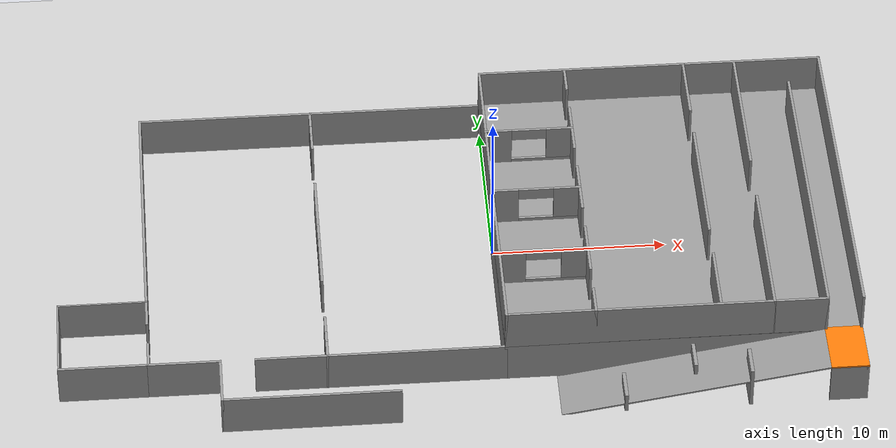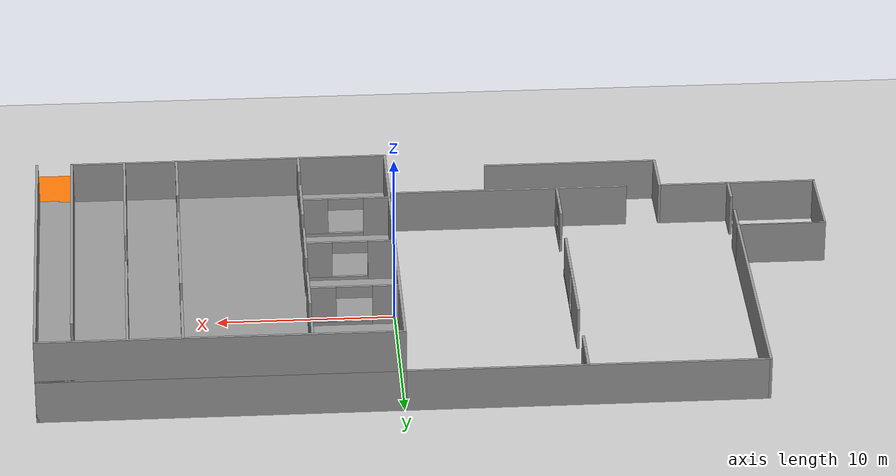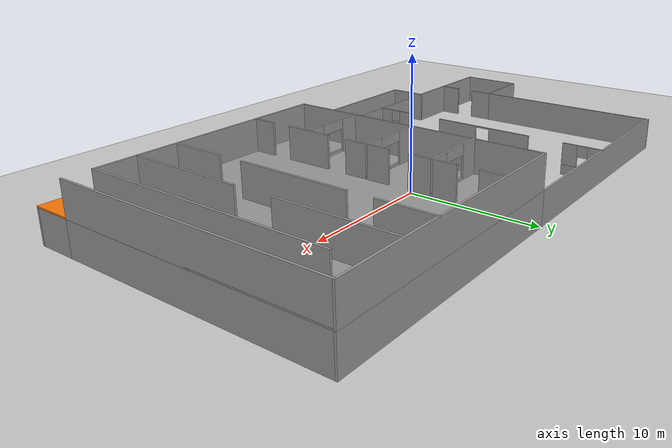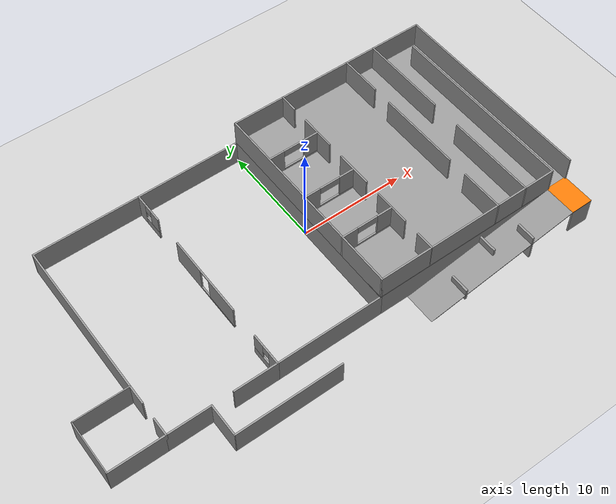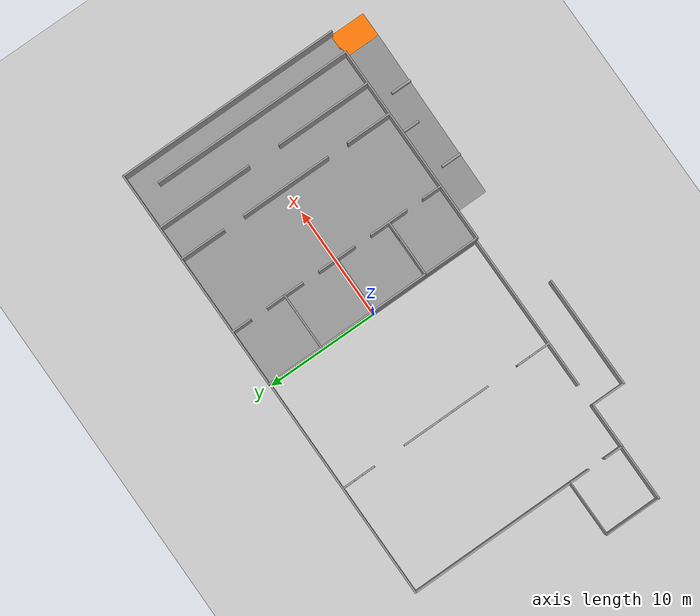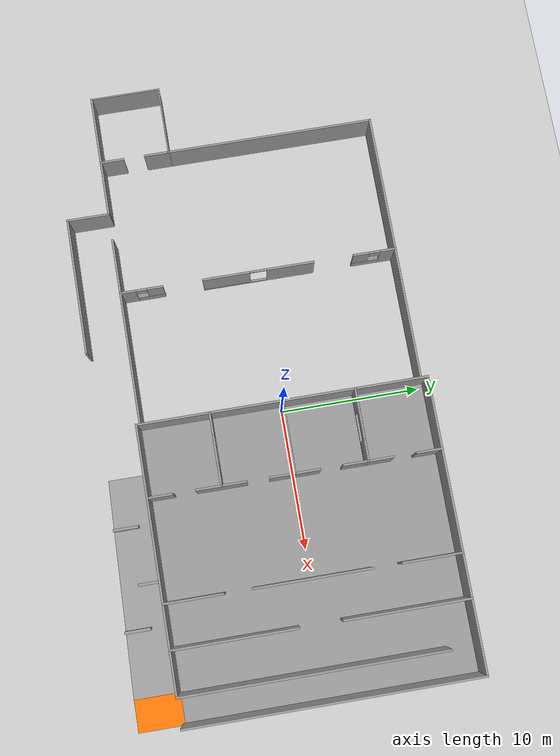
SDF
<sdf version="1.7">
 <world name="default">
  <light name="sun" type="directional">
   <pose>0 0 10 0 -0 0</pose>
   <diffuse>0.8 0.8 0.8 1</diffuse>
   <specular>0.2 0.2 0.2 1</specular>
   <attenuation>
    <range>1000</range>
    <constant>0.9</constant>
    <linear>0.01</linear>
    <quadratic>0.001</quadratic>
   </attenuation>
   <direction>-0.5 0.1 -0.9</direction>
   <spot><inner_angle>0</inner_angle><outer_angle>0</outer_angle><falloff>0</falloff></spot>
  </light>
  <model name="ground_plane">
   <static>1</static>
   <link name="link">
    <collision name="collision">
     <geometry><plane><normal>0 0 1</normal><size>100 100</size></plane></geometry>
     <surface>
      <contact><collide_bitmask>65535</collide_bitmask></contact>
      <friction><ode><mu>100</mu><mu2>50</mu2></ode></friction>
     </surface>
    </collision>
    <visual name="visual">
     <cast_shadows>0</cast_shadows>
     <geometry><plane><normal>0 0 1</normal><size>100 100</size></plane></geometry>
     <material>
      <script><uri>file://media/materials/scripts/gazebo.material</uri><name>Gazebo/Grey</name></script>
     </material>
    </visual>
   </link>
  </model>
  <gravity>0 0 -9.8</gravity>
  <magnetic_field>6e-06 2.3e-05 -4.2e-05</magnetic_field>
  <atmosphere type="adiabatic"/>
  <physics type="ode">
   <max_step_size>0.001</max_step_size>
   <real_time_factor>1</real_time_factor>
   <real_time_update_rate>1000</real_time_update_rate>
  </physics>
  <scene><ambient>0.4 0.4 0.4 1</ambient><background>0.7 0.7 0.7 1</background><shadows>1</shadows></scene>
  <spherical_coordinates>
   <surface_model>EARTH_WGS84</surface_model>
   <latitude_deg>0</latitude_deg>
   <longitude_deg>0</longitude_deg>
   <elevation>0</elevation>
   <heading_deg>0</heading_deg>
  </spherical_coordinates>
  <plugin name="object_spawner_gz_plugin" filename="libobject_spawner_gz_plugin.so"/>
  <model name="smart_house_3_0">
   <link name="Floor_5">
    <pose>21.4845 -10.0155 2.5 0 -0 0</pose>
    <inertial>
     <inertia><ixx>1</ixx><ixy>0</ixy><ixz>0</ixz><iyy>1</iyy><iyz>0</iyz><izz>1</izz></inertia>
     <mass>1</mass>
    </inertial>
    <visual name="Floor_5_Visual">
     <pose>0 0 0.05 0 -0 0</pose>
     <geometry><box><size>2.15 3.15 0.1</size></box></geometry>
     <material>
      <script><uri>file://media/materials/scripts/gazebo.material</uri><name>Gazebo/Grey</name></script>
      <ambient>0.996078 0.47451 0.0196078 1</ambient>
      <shader type="pixel"/>
     </material>
     <meta><layer>1</layer></meta>
    </visual>
    <collision name="Floor_5_Collision">
     <pose>0 0 0.05 0 -0 0</pose>
     <geometry><box><size>2.15 3.15 0.1</size></box></geometry>
     <surface>
      <friction>
       <ode><mu>1</mu><mu2>1</mu2><fdir1>0 0 0</fdir1><slip1>0</slip1><slip2>0</slip2></ode>
       <torsional>
        <coefficient>1</coefficient>
        <patch_radius>0</patch_radius>
        <surface_radius>0</surface_radius>
        <use_patch_radius>1</use_patch_radius>
        <ode><slip>0</slip></ode>
       </torsional>
      </friction>
      <bounce><restitution_coefficient>0</restitution_coefficient><threshold>1e+06</threshold></bounce>
      <contact>
       <collide_without_contact>0</collide_without_contact>
       <collide_without_contact_bitmask>1</collide_without_contact_bitmask>
       <collide_bitmask>1</collide_bitmask>
       <ode>
        <soft_cfm>0</soft_cfm>
        <soft_erp>0.2</soft_erp>
        <kp>1e+13</kp>
        <kd>1</kd>
        <max_vel>0.01</max_vel>
        <min_depth>0</min_depth>
       </ode>
       <bullet>
        <split_impulse>1</split_impulse>
        <split_impulse_penetration_threshold>-0.01</split_impulse_penetration_threshold>
        <soft_cfm>0</soft_cfm>
        <soft_erp>0.2</soft_erp>
        <kp>1e+13</kp>
        <kd>1</kd>
       </bullet>
      </contact>
     </surface>
    </collision>
   </link>
   <link name="Floor_6">
    <pose>12.4845 1.48447 2.5 0 -0 0</pose>
    <inertial>
     <inertia><ixx>1</ixx><ixy>0</ixy><ixz>0</ixz><iyy>1</iyy><iyz>0</iyz><izz>1</izz></inertia>
     <mass>1</mass>
    </inertial>
    <visual name="Floor_6_Visual">
     <pose>0 0 0.05 0 -0 0</pose>
     <geometry><box><size>20.15 20.15 0.1</size></box></geometry>
     <material>
      <script><uri>file://media/materials/scripts/gazebo.material</uri><name>Gazebo/Grey</name></script>
      <ambient>1 1 1 1</ambient>
      <shader type="pixel"/>
     </material>
     <meta><layer>2</layer></meta>
    </visual>
    <collision name="Floor_6_Collision">
     <pose>0 0 0.05 0 -0 0</pose>
     <geometry><box><size>20.15 20.15 0.1</size></box></geometry>
     <surface>
      <friction>
       <ode><mu>1</mu><mu2>1</mu2><fdir1>0 0 0</fdir1><slip1>0</slip1><slip2>0</slip2></ode>
       <torsional>
        <coefficient>1</coefficient>
        <patch_radius>0</patch_radius>
        <surface_radius>0</surface_radius>
        <use_patch_radius>1</use_patch_radius>
        <ode><slip>0</slip></ode>
       </torsional>
      </friction>
      <bounce><restitution_coefficient>0</restitution_coefficient><threshold>1e+06</threshold></bounce>
      <contact>
       <collide_without_contact>0</collide_without_contact>
       <collide_without_contact_bitmask>1</collide_without_contact_bitmask>
       <collide_bitmask>1</collide_bitmask>
       <ode>
        <soft_cfm>0</soft_cfm>
        <soft_erp>0.2</soft_erp>
        <kp>1e+13</kp>
        <kd>1</kd>
        <max_vel>0.01</max_vel>
        <min_depth>0</min_depth>
       </ode>
       <bullet>
        <split_impulse>1</split_impulse>
        <split_impulse_penetration_threshold>-0.01</split_impulse_penetration_threshold>
        <soft_cfm>0</soft_cfm>
        <soft_erp>0.2</soft_erp>
        <kp>1e+13</kp>
        <kd>1</kd>
       </bullet>
      </contact>
     </surface>
    </collision>
   </link>
   <link name="Wall_11">
    <pose>-20.0155 -3.51553 0 0 -0 3.14159</pose>
    <inertial>
     <inertia><ixx>1</ixx><ixy>0</ixy><ixz>0</ixz><iyy>1</iyy><iyz>0</iyz><izz>1</izz></inertia>
     <mass>1</mass>
    </inertial>
    <visual name="Wall_11_Visual">
     <pose>0 0 1.25 0 -0 0</pose>
     <geometry><box><size>5.1 0.1 2.5</size></box></geometry>
     <material>
      <script><uri>file://media/materials/scripts/gazebo.material</uri><name>Gazebo/Grey</name></script>
      <ambient>1 1 1 1</ambient>
      <shader type="pixel"/>
     </material>
     <meta><layer>0</layer></meta>
    </visual>
    <collision name="Wall_11_Collision">
     <pose>0 0 1.25 0 -0 0</pose>
     <geometry><box><size>5.1 0.1 2.5</size></box></geometry>
     <surface>
      <friction>
       <ode><mu>1</mu><mu2>1</mu2><fdir1>0 0 0</fdir1><slip1>0</slip1><slip2>0</slip2></ode>
       <torsional>
        <coefficient>1</coefficient>
        <patch_radius>0</patch_radius>
        <surface_radius>0</surface_radius>
        <use_patch_radius>1</use_patch_radius>
        <ode><slip>0</slip></ode>
       </torsional>
      </friction>
      <bounce><restitution_coefficient>0</restitution_coefficient><threshold>1e+06</threshold></bounce>
      <contact>
       <collide_without_contact>0</collide_without_contact>
       <collide_without_contact_bitmask>1</collide_without_contact_bitmask>
       <collide_bitmask>1</collide_bitmask>
       <ode>
        <soft_cfm>0</soft_cfm>
        <soft_erp>0.2</soft_erp>
        <kp>1e+13</kp>
        <kd>1</kd>
        <max_vel>0.01</max_vel>
        <min_depth>0</min_depth>
       </ode>
       <bullet>
        <split_impulse>1</split_impulse>
        <split_impulse_penetration_threshold>-0.01</split_impulse_penetration_threshold>
        <soft_cfm>0</soft_cfm>
        <soft_erp>0.2</soft_erp>
        <kp>1e+13</kp>
        <kd>1</kd>
       </bullet>
      </contact>
     </surface>
    </collision>
   </link>
   <link name="Wall_12">
    <pose>-22.5155 -6.01553 0 0 0 -1.5708</pose>
    <inertial>
     <inertia><ixx>1</ixx><ixy>0</ixy><ixz>0</ixz><iyy>1</iyy><iyz>0</iyz><izz>1</izz></inertia>
     <mass>1</mass>
    </inertial>
    <visual name="Wall_12_Visual">
     <pose>0 0 1.25 0 -0 0</pose>
     <geometry><box><size>5.1 0.1 2.5</size></box></geometry>
     <material>
      <script><uri>file://media/materials/scripts/gazebo.material</uri><name>Gazebo/Grey</name></script>
      <ambient>1 1 1 1</ambient>
      <shader type="pixel"/>
     </material>
     <meta><layer>0</layer></meta>
    </visual>
    <collision name="Wall_12_Collision">
     <pose>0 0 1.25 0 -0 0</pose>
     <geometry><box><size>5.1 0.1 2.5</size></box></geometry>
     <surface>
      <friction>
       <ode><mu>1</mu><mu2>1</mu2><fdir1>0 0 0</fdir1><slip1>0</slip1><slip2>0</slip2></ode>
       <torsional>
        <coefficient>1</coefficient>
        <patch_radius>0</patch_radius>
        <surface_radius>0</surface_radius>
        <use_patch_radius>1</use_patch_radius>
        <ode><slip>0</slip></ode>
       </torsional>
      </friction>
      <bounce><restitution_coefficient>0</restitution_coefficient><threshold>1e+06</threshold></bounce>
      <contact>
       <collide_without_contact>0</collide_without_contact>
       <collide_without_contact_bitmask>1</collide_without_contact_bitmask>
       <collide_bitmask>1</collide_bitmask>
       <ode>
        <soft_cfm>0</soft_cfm>
        <soft_erp>0.2</soft_erp>
        <kp>1e+13</kp>
        <kd>1</kd>
        <max_vel>0.01</max_vel>
        <min_depth>0</min_depth>
       </ode>
       <bullet>
        <split_impulse>1</split_impulse>
        <split_impulse_penetration_threshold>-0.01</split_impulse_penetration_threshold>
        <soft_cfm>0</soft_cfm>
        <soft_erp>0.2</soft_erp>
        <kp>1e+13</kp>
        <kd>1</kd>
       </bullet>
      </contact>
     </surface>
    </collision>
   </link>
   <link name="Wall_14">
    <pose>2.48447 1.48447 0 0 -0 1.5708</pose>
    <inertial>
     <inertia><ixx>1</ixx><ixy>0</ixy><ixz>0</ixz><iyy>1</iyy><iyz>0</iyz><izz>1</izz></inertia>
     <mass>1</mass>
    </inertial>
    <visual name="Wall_14_Visual">
     <pose>0 0 1.25 0 -0 0</pose>
     <geometry><box><size>20.15 0.15 2.5</size></box></geometry>
     <material>
      <script><uri>file://media/materials/scripts/gazebo.material</uri><name>Gazebo/Grey</name></script>
      <ambient>1 1 1 1</ambient>
      <shader type="pixel"/>
     </material>
     <meta><layer>0</layer></meta>
    </visual>
    <collision name="Wall_14_Collision">
     <pose>0 0 1.25 0 -0 0</pose>
     <geometry><box><size>20.15 0.15 2.5</size></box></geometry>
     <surface>
      <friction>
       <ode><mu>1</mu><mu2>1</mu2><fdir1>0 0 0</fdir1><slip1>0</slip1><slip2>0</slip2></ode>
       <torsional>
        <coefficient>1</coefficient>
        <patch_radius>0</patch_radius>
        <surface_radius>0</surface_radius>
        <use_patch_radius>1</use_patch_radius>
        <ode><slip>0</slip></ode>
       </torsional>
      </friction>
      <bounce><restitution_coefficient>0</restitution_coefficient><threshold>1e+06</threshold></bounce>
      <contact>
       <collide_without_contact>0</collide_without_contact>
       <collide_without_contact_bitmask>1</collide_without_contact_bitmask>
       <collide_bitmask>1</collide_bitmask>
       <ode>
        <soft_cfm>0</soft_cfm>
        <soft_erp>0.2</soft_erp>
        <kp>1e+13</kp>
        <kd>1</kd>
        <max_vel>0.01</max_vel>
        <min_depth>0</min_depth>
       </ode>
       <bullet>
        <split_impulse>1</split_impulse>
        <split_impulse_penetration_threshold>-0.01</split_impulse_penetration_threshold>
        <soft_cfm>0</soft_cfm>
        <soft_erp>0.2</soft_erp>
        <kp>1e+13</kp>
        <kd>1</kd>
       </bullet>
      </contact>
     </surface>
    </collision>
   </link>
   <link name="Wall_15">
    <pose>-7.51553 11.4845 0 0 -0 3.14159</pose>
    <inertial>
     <inertia><ixx>1</ixx><ixy>0</ixy><ixz>0</ixz><iyy>1</iyy><iyz>0</iyz><izz>1</izz></inertia>
     <mass>1</mass>
    </inertial>
    <visual name="Wall_15_Visual">
     <pose>0 0 1.25 0 -0 0</pose>
     <geometry><box><size>20.15 0.15 2.5</size></box></geometry>
     <material>
      <script><uri>file://media/materials/scripts/gazebo.material</uri><name>Gazebo/Grey</name></script>
      <ambient>1 1 1 1</ambient>
      <shader type="pixel"/>
     </material>
     <meta><layer>0</layer></meta>
    </visual>
    <collision name="Wall_15_Collision">
     <pose>0 0 1.25 0 -0 0</pose>
     <geometry><box><size>20.15 0.15 2.5</size></box></geometry>
     <surface>
      <friction>
       <ode><mu>1</mu><mu2>1</mu2><fdir1>0 0 0</fdir1><slip1>0</slip1><slip2>0</slip2></ode>
       <torsional>
        <coefficient>1</coefficient>
        <patch_radius>0</patch_radius>
        <surface_radius>0</surface_radius>
        <use_patch_radius>1</use_patch_radius>
        <ode><slip>0</slip></ode>
       </torsional>
      </friction>
      <bounce><restitution_coefficient>0</restitution_coefficient><threshold>1e+06</threshold></bounce>
      <contact>
       <collide_without_contact>0</collide_without_contact>
       <collide_without_contact_bitmask>1</collide_without_contact_bitmask>
       <collide_bitmask>1</collide_bitmask>
       <ode>
        <soft_cfm>0</soft_cfm>
        <soft_erp>0.2</soft_erp>
        <kp>1e+13</kp>
        <kd>1</kd>
        <max_vel>0.01</max_vel>
        <min_depth>0</min_depth>
       </ode>
       <bullet>
        <split_impulse>1</split_impulse>
        <split_impulse_penetration_threshold>-0.01</split_impulse_penetration_threshold>
        <soft_cfm>0</soft_cfm>
        <soft_erp>0.2</soft_erp>
        <kp>1e+13</kp>
        <kd>1</kd>
       </bullet>
      </contact>
     </surface>
    </collision>
   </link>
   <link name="Wall_16">
    <pose>-17.5155 3.98447 0 0 0 -1.5708</pose>
    <inertial>
     <inertia><ixx>1</ixx><ixy>0</ixy><ixz>0</ixz><iyy>1</iyy><iyz>0</iyz><izz>1</izz></inertia>
     <mass>1</mass>
    </inertial>
    <visual name="Wall_16_Visual">
     <pose>0 0 1.25 0 -0 0</pose>
     <geometry><box><size>15.1503 0.15 2.5</size></box></geometry>
     <material>
      <script><uri>file://media/materials/scripts/gazebo.material</uri><name>Gazebo/Grey</name></script>
      <ambient>1 1 1 1</ambient>
      <shader type="pixel"/>
     </material>
     <meta><layer>0</layer></meta>
    </visual>
    <collision name="Wall_16_Collision">
     <pose>0 0 1.25 0 -0 0</pose>
     <geometry><box><size>15.1503 0.15 2.5</size></box></geometry>
     <surface>
      <friction>
       <ode><mu>1</mu><mu2>1</mu2><fdir1>0 0 0</fdir1><slip1>0</slip1><slip2>0</slip2></ode>
       <torsional>
        <coefficient>1</coefficient>
        <patch_radius>0</patch_radius>
        <surface_radius>0</surface_radius>
        <use_patch_radius>1</use_patch_radius>
        <ode><slip>0</slip></ode>
       </torsional>
      </friction>
      <bounce><restitution_coefficient>0</restitution_coefficient><threshold>1e+06</threshold></bounce>
      <contact>
       <collide_without_contact>0</collide_without_contact>
       <collide_without_contact_bitmask>1</collide_without_contact_bitmask>
       <collide_bitmask>1</collide_bitmask>
       <ode>
        <soft_cfm>0</soft_cfm>
        <soft_erp>0.2</soft_erp>
        <kp>1e+13</kp>
        <kd>1</kd>
        <max_vel>0.01</max_vel>
        <min_depth>0</min_depth>
       </ode>
       <bullet>
        <split_impulse>1</split_impulse>
        <split_impulse_penetration_threshold>-0.01</split_impulse_penetration_threshold>
        <soft_cfm>0</soft_cfm>
        <soft_erp>0.2</soft_erp>
        <kp>1e+13</kp>
        <kd>1</kd>
       </bullet>
      </contact>
     </surface>
    </collision>
   </link>
   <link name="Wall_19">
    <pose>22.4845 1.48447 0 0 -0 1.5708</pose>
    <inertial>
     <inertia><ixx>1</ixx><ixy>0</ixy><ixz>0</ixz><iyy>1</iyy><iyz>0</iyz><izz>1</izz></inertia>
     <mass>1</mass>
    </inertial>
    <visual name="Wall_19_Visual">
     <pose>0 0 1.25 0 -0 0</pose>
     <geometry><box><size>20.15 0.15 2.5</size></box></geometry>
     <material>
      <script><uri>file://media/materials/scripts/gazebo.material</uri><name>Gazebo/Grey</name></script>
      <ambient>1 1 1 1</ambient>
      <shader type="pixel"/>
     </material>
     <meta><layer>0</layer></meta>
    </visual>
    <collision name="Wall_19_Collision">
     <pose>0 0 1.25 0 -0 0</pose>
     <geometry><box><size>20.15 0.15 2.5</size></box></geometry>
     <surface>
      <friction>
       <ode><mu>1</mu><mu2>1</mu2><fdir1>0 0 0</fdir1><slip1>0</slip1><slip2>0</slip2></ode>
       <torsional>
        <coefficient>1</coefficient>
        <patch_radius>0</patch_radius>
        <surface_radius>0</surface_radius>
        <use_patch_radius>1</use_patch_radius>
        <ode><slip>0</slip></ode>
       </torsional>
      </friction>
      <bounce><restitution_coefficient>0</restitution_coefficient><threshold>1e+06</threshold></bounce>
      <contact>
       <collide_without_contact>0</collide_without_contact>
       <collide_without_contact_bitmask>1</collide_without_contact_bitmask>
       <collide_bitmask>1</collide_bitmask>
       <ode>
        <soft_cfm>0</soft_cfm>
        <soft_erp>0.2</soft_erp>
        <kp>1e+13</kp>
        <kd>1</kd>
        <max_vel>0.01</max_vel>
        <min_depth>0</min_depth>
       </ode>
       <bullet>
        <split_impulse>1</split_impulse>
        <split_impulse_penetration_threshold>-0.01</split_impulse_penetration_threshold>
        <soft_cfm>0</soft_cfm>
        <soft_erp>0.2</soft_erp>
        <kp>1e+13</kp>
        <kd>1</kd>
       </bullet>
      </contact>
     </surface>
    </collision>
   </link>
   <link name="Wall_20">
    <pose>12.4845 11.4845 0 0 -0 3.14159</pose>
    <inertial>
     <inertia><ixx>1</ixx><ixy>0</ixy><ixz>0</ixz><iyy>1</iyy><iyz>0</iyz><izz>1</izz></inertia>
     <mass>1</mass>
    </inertial>
    <visual name="Wall_20_Visual">
     <pose>0 0 1.25 0 -0 0</pose>
     <geometry><box><size>20.15 0.15 2.5</size></box></geometry>
     <material>
      <script><uri>file://media/materials/scripts/gazebo.material</uri><name>Gazebo/Grey</name></script>
      <ambient>1 1 1 1</ambient>
      <shader type="pixel"/>
     </material>
     <meta><layer>0</layer></meta>
    </visual>
    <collision name="Wall_20_Collision">
     <pose>0 0 1.25 0 -0 0</pose>
     <geometry><box><size>20.15 0.15 2.5</size></box></geometry>
     <surface>
      <friction>
       <ode><mu>1</mu><mu2>1</mu2><fdir1>0 0 0</fdir1><slip1>0</slip1><slip2>0</slip2></ode>
       <torsional>
        <coefficient>1</coefficient>
        <patch_radius>0</patch_radius>
        <surface_radius>0</surface_radius>
        <use_patch_radius>1</use_patch_radius>
        <ode><slip>0</slip></ode>
       </torsional>
      </friction>
      <bounce><restitution_coefficient>0</restitution_coefficient><threshold>1e+06</threshold></bounce>
      <contact>
       <collide_without_contact>0</collide_without_contact>
       <collide_without_contact_bitmask>1</collide_without_contact_bitmask>
       <collide_bitmask>1</collide_bitmask>
       <ode>
        <soft_cfm>0</soft_cfm>
        <soft_erp>0.2</soft_erp>
        <kp>1e+13</kp>
        <kd>1</kd>
        <max_vel>0.01</max_vel>
        <min_depth>0</min_depth>
       </ode>
       <bullet>
        <split_impulse>1</split_impulse>
        <split_impulse_penetration_threshold>-0.01</split_impulse_penetration_threshold>
        <soft_cfm>0</soft_cfm>
        <soft_erp>0.2</soft_erp>
        <kp>1e+13</kp>
        <kd>1</kd>
       </bullet>
      </contact>
     </surface>
    </collision>
   </link>
   <link name="Wall_226">
    <pose>22.4845 -10.0155 2.5 0 0 -1.5708</pose>
    <inertial>
     <inertia><ixx>1</ixx><ixy>0</ixy><ixz>0</ixz><iyy>1</iyy><iyz>0</iyz><izz>1</izz></inertia>
     <mass>1</mass>
    </inertial>
    <visual name="Wall_226_Visual">
     <geometry><box><size>3.15 0.15 0</size></box></geometry>
     <material>
      <script><uri>file://media/materials/scripts/gazebo.material</uri><name>Gazebo/Grey</name></script>
      <ambient>1 1 1 1</ambient>
      <shader type="pixel"/>
     </material>
     <meta><layer>1</layer></meta>
    </visual>
    <collision name="Wall_226_Collision">
     <geometry><box><size>3.15 0.15 0</size></box></geometry>
     <surface>
      <friction>
       <ode><mu>1</mu><mu2>1</mu2><fdir1>0 0 0</fdir1><slip1>0</slip1><slip2>0</slip2></ode>
       <torsional>
        <coefficient>1</coefficient>
        <patch_radius>0</patch_radius>
        <surface_radius>0</surface_radius>
        <use_patch_radius>1</use_patch_radius>
        <ode><slip>0</slip></ode>
       </torsional>
      </friction>
      <bounce><restitution_coefficient>0</restitution_coefficient><threshold>1e+06</threshold></bounce>
      <contact>
       <collide_without_contact>0</collide_without_contact>
       <collide_without_contact_bitmask>1</collide_without_contact_bitmask>
       <collide_bitmask>1</collide_bitmask>
       <ode>
        <soft_cfm>0</soft_cfm>
        <soft_erp>0.2</soft_erp>
        <kp>1e+13</kp>
        <kd>1</kd>
        <max_vel>0.01</max_vel>
        <min_depth>0</min_depth>
       </ode>
       <bullet>
        <split_impulse>1</split_impulse>
        <split_impulse_penetration_threshold>-0.01</split_impulse_penetration_threshold>
        <soft_cfm>0</soft_cfm>
        <soft_erp>0.2</soft_erp>
        <kp>1e+13</kp>
        <kd>1</kd>
       </bullet>
      </contact>
     </surface>
    </collision>
   </link>
   <link name="Wall_227">
    <pose>21.4845 -11.5155 2.5 0 -0 3.14159</pose>
    <inertial>
     <inertia><ixx>1</ixx><ixy>0</ixy><ixz>0</ixz><iyy>1</iyy><iyz>0</iyz><izz>1</izz></inertia>
     <mass>1</mass>
    </inertial>
    <visual name="Wall_227_Visual">
     <geometry><box><size>2.15 0.15 0</size></box></geometry>
     <material>
      <script><uri>file://media/materials/scripts/gazebo.material</uri><name>Gazebo/Grey</name></script>
      <ambient>1 1 1 1</ambient>
      <shader type="pixel"/>
     </material>
     <meta><layer>1</layer></meta>
    </visual>
    <collision name="Wall_227_Collision">
     <geometry><box><size>2.15 0.15 0</size></box></geometry>
     <surface>
      <friction>
       <ode><mu>1</mu><mu2>1</mu2><fdir1>0 0 0</fdir1><slip1>0</slip1><slip2>0</slip2></ode>
       <torsional>
        <coefficient>1</coefficient>
        <patch_radius>0</patch_radius>
        <surface_radius>0</surface_radius>
        <use_patch_radius>1</use_patch_radius>
        <ode><slip>0</slip></ode>
       </torsional>
      </friction>
      <bounce><restitution_coefficient>0</restitution_coefficient><threshold>1e+06</threshold></bounce>
      <contact>
       <collide_without_contact>0</collide_without_contact>
       <collide_without_contact_bitmask>1</collide_without_contact_bitmask>
       <collide_bitmask>1</collide_bitmask>
       <ode>
        <soft_cfm>0</soft_cfm>
        <soft_erp>0.2</soft_erp>
        <kp>1e+13</kp>
        <kd>1</kd>
        <max_vel>0.01</max_vel>
        <min_depth>0</min_depth>
       </ode>
       <bullet>
        <split_impulse>1</split_impulse>
        <split_impulse_penetration_threshold>-0.01</split_impulse_penetration_threshold>
        <soft_cfm>0</soft_cfm>
        <soft_erp>0.2</soft_erp>
        <kp>1e+13</kp>
        <kd>1</kd>
       </bullet>
      </contact>
     </surface>
    </collision>
   </link>
   <link name="Wall_234">
    <pose>2.48447 1.48447 2.5 0 -0 1.5708</pose>
    <inertial>
     <inertia><ixx>1</ixx><ixy>0</ixy><ixz>0</ixz><iyy>1</iyy><iyz>0</iyz><izz>1</izz></inertia>
     <mass>1</mass>
    </inertial>
    <visual name="Wall_234_Visual">
     <pose>0 0 1.25 0 -0 0</pose>
     <geometry><box><size>20.15 0.15 2.5</size></box></geometry>
     <material>
      <script><uri>file://media/materials/scripts/gazebo.material</uri><name>Gazebo/Grey</name></script>
      <ambient>1 1 1 1</ambient>
      <shader type="pixel"/>
     </material>
     <meta><layer>2</layer></meta>
    </visual>
    <collision name="Wall_234_Collision">
     <pose>0 0 1.25 0 -0 0</pose>
     <geometry><box><size>20.15 0.15 2.5</size></box></geometry>
     <surface>
      <friction>
       <ode><mu>1</mu><mu2>1</mu2><fdir1>0 0 0</fdir1><slip1>0</slip1><slip2>0</slip2></ode>
       <torsional>
        <coefficient>1</coefficient>
        <patch_radius>0</patch_radius>
        <surface_radius>0</surface_radius>
        <use_patch_radius>1</use_patch_radius>
        <ode><slip>0</slip></ode>
       </torsional>
      </friction>
      <bounce><restitution_coefficient>0</restitution_coefficient><threshold>1e+06</threshold></bounce>
      <contact>
       <collide_without_contact>0</collide_without_contact>
       <collide_without_contact_bitmask>1</collide_without_contact_bitmask>
       <collide_bitmask>1</collide_bitmask>
       <ode>
        <soft_cfm>0</soft_cfm>
        <soft_erp>0.2</soft_erp>
        <kp>1e+13</kp>
        <kd>1</kd>
        <max_vel>0.01</max_vel>
        <min_depth>0</min_depth>
       </ode>
       <bullet>
        <split_impulse>1</split_impulse>
        <split_impulse_penetration_threshold>-0.01</split_impulse_penetration_threshold>
        <soft_cfm>0</soft_cfm>
        <soft_erp>0.2</soft_erp>
        <kp>1e+13</kp>
        <kd>1</kd>
       </bullet>
      </contact>
     </surface>
    </collision>
   </link>
   <link name="Wall_237">
    <pose>22.4845 1.48447 2.5 0 -0 1.5708</pose>
    <inertial>
     <inertia><ixx>1</ixx><ixy>0</ixy><ixz>0</ixz><iyy>1</iyy><iyz>0</iyz><izz>1</izz></inertia>
     <mass>1</mass>
    </inertial>
    <visual name="Wall_237_Visual">
     <pose>0 0 1.25 0 -0 0</pose>
     <geometry><box><size>20.15 0.15 2.5</size></box></geometry>
     <material>
      <script><uri>file://media/materials/scripts/gazebo.material</uri><name>Gazebo/Grey</name></script>
      <ambient>1 1 1 1</ambient>
      <shader type="pixel"/>
     </material>
     <meta><layer>2</layer></meta>
    </visual>
    <collision name="Wall_237_Collision">
     <pose>0 0 1.25 0 -0 0</pose>
     <geometry><box><size>20.15 0.15 2.5</size></box></geometry>
     <surface>
      <friction>
       <ode><mu>1</mu><mu2>1</mu2><fdir1>0 0 0</fdir1><slip1>0</slip1><slip2>0</slip2></ode>
       <torsional>
        <coefficient>1</coefficient>
        <patch_radius>0</patch_radius>
        <surface_radius>0</surface_radius>
        <use_patch_radius>1</use_patch_radius>
        <ode><slip>0</slip></ode>
       </torsional>
      </friction>
      <bounce><restitution_coefficient>0</restitution_coefficient><threshold>1e+06</threshold></bounce>
      <contact>
       <collide_without_contact>0</collide_without_contact>
       <collide_without_contact_bitmask>1</collide_without_contact_bitmask>
       <collide_bitmask>1</collide_bitmask>
       <ode>
        <soft_cfm>0</soft_cfm>
        <soft_erp>0.2</soft_erp>
        <kp>1e+13</kp>
        <kd>1</kd>
        <max_vel>0.01</max_vel>
        <min_depth>0</min_depth>
       </ode>
       <bullet>
        <split_impulse>1</split_impulse>
        <split_impulse_penetration_threshold>-0.01</split_impulse_penetration_threshold>
        <soft_cfm>0</soft_cfm>
        <soft_erp>0.2</soft_erp>
        <kp>1e+13</kp>
        <kd>1</kd>
       </bullet>
      </contact>
     </surface>
    </collision>
   </link>
   <link name="Wall_238">
    <pose>12.4845 11.4845 2.5 0 -0 3.14159</pose>
    <inertial>
     <inertia><ixx>1</ixx><ixy>0</ixy><ixz>0</ixz><iyy>1</iyy><iyz>0</iyz><izz>1</izz></inertia>
     <mass>1</mass>
    </inertial>
    <visual name="Wall_238_Visual">
     <pose>0 0 1.25 0 -0 0</pose>
     <geometry><box><size>20.15 0.15 2.5</size></box></geometry>
     <material>
      <script><uri>file://media/materials/scripts/gazebo.material</uri><name>Gazebo/Grey</name></script>
      <ambient>1 1 1 1</ambient>
      <shader type="pixel"/>
     </material>
     <meta><layer>2</layer></meta>
    </visual>
    <collision name="Wall_238_Collision">
     <pose>0 0 1.25 0 -0 0</pose>
     <geometry><box><size>20.15 0.15 2.5</size></box></geometry>
     <surface>
      <friction>
       <ode><mu>1</mu><mu2>1</mu2><fdir1>0 0 0</fdir1><slip1>0</slip1><slip2>0</slip2></ode>
       <torsional>
        <coefficient>1</coefficient>
        <patch_radius>0</patch_radius>
        <surface_radius>0</surface_radius>
        <use_patch_radius>1</use_patch_radius>
        <ode><slip>0</slip></ode>
       </torsional>
      </friction>
      <bounce><restitution_coefficient>0</restitution_coefficient><threshold>1e+06</threshold></bounce>
      <contact>
       <collide_without_contact>0</collide_without_contact>
       <collide_without_contact_bitmask>1</collide_without_contact_bitmask>
       <collide_bitmask>1</collide_bitmask>
       <ode>
        <soft_cfm>0</soft_cfm>
        <soft_erp>0.2</soft_erp>
        <kp>1e+13</kp>
        <kd>1</kd>
        <max_vel>0.01</max_vel>
        <min_depth>0</min_depth>
       </ode>
       <bullet>
        <split_impulse>1</split_impulse>
        <split_impulse_penetration_threshold>-0.01</split_impulse_penetration_threshold>
        <soft_cfm>0</soft_cfm>
        <soft_erp>0.2</soft_erp>
        <kp>1e+13</kp>
        <kd>1</kd>
       </bullet>
      </contact>
     </surface>
    </collision>
   </link>
   <link name="Wall_24">
    <pose>-17.5155 -6.01553 0 0 0 -1.5708</pose>
    <inertial>
     <inertia><ixx>1</ixx><ixy>0</ixy><ixz>0</ixz><iyy>1</iyy><iyz>0</iyz><izz>1</izz></inertia>
     <mass>1</mass>
    </inertial>
    <visual name="Wall_24_Visual_0">
     <pose>-1.63657 0 1.25 0 -0 0</pose>
     <geometry><box><size>1.87687 0.15 2.5</size></box></geometry>
     <material>
      <script><uri>file://media/materials/scripts/gazebo.material</uri><name>Gazebo/Grey</name></script>
      <ambient>1 1 1 1</ambient>
      <shader type="pixel"/>
     </material>
     <meta><layer>0</layer></meta>
    </visual>
    <visual name="Wall_24_Visual_1">
     <pose>1.68843 0 1.25 0 -0 0</pose>
     <geometry><box><size>1.77313 0.15 2.5</size></box></geometry>
     <material>
      <script><uri>file://media/materials/scripts/gazebo.material</uri><name>Gazebo/Grey</name></script>
      <ambient>1 1 1 1</ambient>
      <shader type="pixel"/>
     </material>
     <meta><layer>0</layer></meta>
    </visual>
    <collision name="Wall_24_Collision_0">
     <pose>-1.63657 0 1.25 0 -0 0</pose>
     <geometry><box><size>1.87687 0.15 2.5</size></box></geometry>
     <surface>
      <friction>
       <ode><mu>1</mu><mu2>1</mu2><fdir1>0 0 0</fdir1><slip1>0</slip1><slip2>0</slip2></ode>
       <torsional>
        <coefficient>1</coefficient>
        <patch_radius>0</patch_radius>
        <surface_radius>0</surface_radius>
        <use_patch_radius>1</use_patch_radius>
        <ode><slip>0</slip></ode>
       </torsional>
      </friction>
      <bounce><restitution_coefficient>0</restitution_coefficient><threshold>1e+06</threshold></bounce>
      <contact>
       <collide_without_contact>0</collide_without_contact>
       <collide_without_contact_bitmask>1</collide_without_contact_bitmask>
       <collide_bitmask>1</collide_bitmask>
       <ode>
        <soft_cfm>0</soft_cfm>
        <soft_erp>0.2</soft_erp>
        <kp>1e+13</kp>
        <kd>1</kd>
        <max_vel>0.01</max_vel>
        <min_depth>0</min_depth>
       </ode>
       <bullet>
        <split_impulse>1</split_impulse>
        <split_impulse_penetration_threshold>-0.01</split_impulse_penetration_threshold>
        <soft_cfm>0</soft_cfm>
        <soft_erp>0.2</soft_erp>
        <kp>1e+13</kp>
        <kd>1</kd>
       </bullet>
      </contact>
     </surface>
    </collision>
    <collision name="Wall_24_Collision_1">
     <pose>1.68843 0 1.25 0 -0 0</pose>
     <geometry><box><size>1.77313 0.15 2.5</size></box></geometry>
     <surface>
      <friction>
       <ode><mu>1</mu><mu2>1</mu2><fdir1>0 0 0</fdir1><slip1>0</slip1><slip2>0</slip2></ode>
       <torsional>
        <coefficient>1</coefficient>
        <patch_radius>0</patch_radius>
        <surface_radius>0</surface_radius>
        <use_patch_radius>1</use_patch_radius>
        <ode><slip>0</slip></ode>
       </torsional>
      </friction>
      <bounce><restitution_coefficient>0</restitution_coefficient><threshold>1e+06</threshold></bounce>
      <contact>
       <collide_without_contact>0</collide_without_contact>
       <collide_without_contact_bitmask>1</collide_without_contact_bitmask>
       <collide_bitmask>1</collide_bitmask>
       <ode>
        <soft_cfm>0</soft_cfm>
        <soft_erp>0.2</soft_erp>
        <kp>1e+13</kp>
        <kd>1</kd>
        <max_vel>0.01</max_vel>
        <min_depth>0</min_depth>
       </ode>
       <bullet>
        <split_impulse>1</split_impulse>
        <split_impulse_penetration_threshold>-0.01</split_impulse_penetration_threshold>
        <soft_cfm>0</soft_cfm>
        <soft_erp>0.2</soft_erp>
        <kp>1e+13</kp>
        <kd>1</kd>
       </bullet>
      </contact>
     </surface>
    </collision>
   </link>
   <link name="Wall_258">
    <pose>11.4845 -8.51553 2.5 0 -0 0</pose>
    <inertial>
     <inertia><ixx>1</ixx><ixy>0</ixy><ixz>0</ixz><iyy>1</iyy><iyz>0</iyz><izz>1</izz></inertia>
     <mass>1</mass>
    </inertial>
    <visual name="Wall_258_Visual">
     <pose>0 0 1.25 0 -0 0</pose>
     <geometry><box><size>18.15 0.15 2.5</size></box></geometry>
     <material>
      <script><uri>file://media/materials/scripts/gazebo.material</uri><name>Gazebo/Grey</name></script>
      <ambient>1 1 1 1</ambient>
      <shader type="pixel"/>
     </material>
     <meta><layer>2</layer></meta>
    </visual>
    <collision name="Wall_258_Collision">
     <pose>0 0 1.25 0 -0 0</pose>
     <geometry><box><size>18.15 0.15 2.5</size></box></geometry>
     <surface>
      <friction>
       <ode><mu>1</mu><mu2>1</mu2><fdir1>0 0 0</fdir1><slip1>0</slip1><slip2>0</slip2></ode>
       <torsional>
        <coefficient>1</coefficient>
        <patch_radius>0</patch_radius>
        <surface_radius>0</surface_radius>
        <use_patch_radius>1</use_patch_radius>
        <ode><slip>0</slip></ode>
       </torsional>
      </friction>
      <bounce><restitution_coefficient>0</restitution_coefficient><threshold>1e+06</threshold></bounce>
      <contact>
       <collide_without_contact>0</collide_without_contact>
       <collide_without_contact_bitmask>1</collide_without_contact_bitmask>
       <collide_bitmask>1</collide_bitmask>
       <ode>
        <soft_cfm>0</soft_cfm>
        <soft_erp>0.2</soft_erp>
        <kp>1e+13</kp>
        <kd>1</kd>
        <max_vel>0.01</max_vel>
        <min_depth>0</min_depth>
       </ode>
       <bullet>
        <split_impulse>1</split_impulse>
        <split_impulse_penetration_threshold>-0.01</split_impulse_penetration_threshold>
        <soft_cfm>0</soft_cfm>
        <soft_erp>0.2</soft_erp>
        <kp>1e+13</kp>
        <kd>1</kd>
       </bullet>
      </contact>
     </surface>
    </collision>
   </link>
   <link name="Wall_265">
    <pose>20.4845 0.484467 2.5 0 -0 1.5708</pose>
    <inertial>
     <inertia><ixx>1</ixx><ixy>0</ixy><ixz>0</ixz><iyy>1</iyy><iyz>0</iyz><izz>1</izz></inertia>
     <mass>1</mass>
    </inertial>
    <visual name="Wall_265_Visual">
     <pose>0 0 1.25 0 -0 0</pose>
     <geometry><box><size>18.15 0.15 2.5</size></box></geometry>
     <material>
      <script><uri>file://media/materials/scripts/gazebo.material</uri><name>Gazebo/Grey</name></script>
      <ambient>1 1 1 1</ambient>
      <shader type="pixel"/>
     </material>
     <meta><layer>2</layer></meta>
    </visual>
    <collision name="Wall_265_Collision">
     <pose>0 0 1.25 0 -0 0</pose>
     <geometry><box><size>18.15 0.15 2.5</size></box></geometry>
     <surface>
      <friction>
       <ode><mu>1</mu><mu2>1</mu2><fdir1>0 0 0</fdir1><slip1>0</slip1><slip2>0</slip2></ode>
       <torsional>
        <coefficient>1</coefficient>
        <patch_radius>0</patch_radius>
        <surface_radius>0</surface_radius>
        <use_patch_radius>1</use_patch_radius>
        <ode><slip>0</slip></ode>
       </torsional>
      </friction>
      <bounce><restitution_coefficient>0</restitution_coefficient><threshold>1e+06</threshold></bounce>
      <contact>
       <collide_without_contact>0</collide_without_contact>
       <collide_without_contact_bitmask>1</collide_without_contact_bitmask>
       <collide_bitmask>1</collide_bitmask>
       <ode>
        <soft_cfm>0</soft_cfm>
        <soft_erp>0.2</soft_erp>
        <kp>1e+13</kp>
        <kd>1</kd>
        <max_vel>0.01</max_vel>
        <min_depth>0</min_depth>
       </ode>
       <bullet>
        <split_impulse>1</split_impulse>
        <split_impulse_penetration_threshold>-0.01</split_impulse_penetration_threshold>
        <soft_cfm>0</soft_cfm>
        <soft_erp>0.2</soft_erp>
        <kp>1e+13</kp>
        <kd>1</kd>
       </bullet>
      </contact>
     </surface>
    </collision>
   </link>
   <link name="Wall_276">
    <pose>17.4845 -4.26553 2.5 0 0 -1.5708</pose>
    <inertial>
     <inertia><ixx>1</ixx><ixy>0</ixy><ixz>0</ixz><iyy>1</iyy><iyz>0</iyz><izz>1</izz></inertia>
     <mass>1</mass>
    </inertial>
    <visual name="Wall_276_Visual">
     <pose>0 0 1.25 0 -0 0</pose>
     <geometry><box><size>8.65 0.15 2.5</size></box></geometry>
     <material>
      <script><uri>file://media/materials/scripts/gazebo.material</uri><name>Gazebo/Grey</name></script>
      <ambient>1 1 1 1</ambient>
      <shader type="pixel"/>
     </material>
     <meta><layer>2</layer></meta>
    </visual>
    <collision name="Wall_276_Collision">
     <pose>0 0 1.25 0 -0 0</pose>
     <geometry><box><size>8.65 0.15 2.5</size></box></geometry>
     <surface>
      <friction>
       <ode><mu>1</mu><mu2>1</mu2><fdir1>0 0 0</fdir1><slip1>0</slip1><slip2>0</slip2></ode>
       <torsional>
        <coefficient>1</coefficient>
        <patch_radius>0</patch_radius>
        <surface_radius>0</surface_radius>
        <use_patch_radius>1</use_patch_radius>
        <ode><slip>0</slip></ode>
       </torsional>
      </friction>
      <bounce><restitution_coefficient>0</restitution_coefficient><threshold>1e+06</threshold></bounce>
      <contact>
       <collide_without_contact>0</collide_without_contact>
       <collide_without_contact_bitmask>1</collide_without_contact_bitmask>
       <collide_bitmask>1</collide_bitmask>
       <ode>
        <soft_cfm>0</soft_cfm>
        <soft_erp>0.2</soft_erp>
        <kp>1e+13</kp>
        <kd>1</kd>
        <max_vel>0.01</max_vel>
        <min_depth>0</min_depth>
       </ode>
       <bullet>
        <split_impulse>1</split_impulse>
        <split_impulse_penetration_threshold>-0.01</split_impulse_penetration_threshold>
        <soft_cfm>0</soft_cfm>
        <soft_erp>0.2</soft_erp>
        <kp>1e+13</kp>
        <kd>1</kd>
       </bullet>
      </contact>
     </surface>
    </collision>
   </link>
   <link name="Wall_278">
    <pose>17.4845 7.23447 2.5 0 -0 1.5708</pose>
    <inertial>
     <inertia><ixx>1</ixx><ixy>0</ixy><ixz>0</ixz><iyy>1</iyy><iyz>0</iyz><izz>1</izz></inertia>
     <mass>1</mass>
    </inertial>
    <visual name="Wall_278_Visual">
     <pose>0 0 1.25 0 -0 0</pose>
     <geometry><box><size>8.65 0.15 2.5</size></box></geometry>
     <material>
      <script><uri>file://media/materials/scripts/gazebo.material</uri><name>Gazebo/Grey</name></script>
      <ambient>1 1 1 1</ambient>
      <shader type="pixel"/>
     </material>
     <meta><layer>2</layer></meta>
    </visual>
    <collision name="Wall_278_Collision">
     <pose>0 0 1.25 0 -0 0</pose>
     <geometry><box><size>8.65 0.15 2.5</size></box></geometry>
     <surface>
      <friction>
       <ode><mu>1</mu><mu2>1</mu2><fdir1>0 0 0</fdir1><slip1>0</slip1><slip2>0</slip2></ode>
       <torsional>
        <coefficient>1</coefficient>
        <patch_radius>0</patch_radius>
        <surface_radius>0</surface_radius>
        <use_patch_radius>1</use_patch_radius>
        <ode><slip>0</slip></ode>
       </torsional>
      </friction>
      <bounce><restitution_coefficient>0</restitution_coefficient><threshold>1e+06</threshold></bounce>
      <contact>
       <collide_without_contact>0</collide_without_contact>
       <collide_without_contact_bitmask>1</collide_without_contact_bitmask>
       <collide_bitmask>1</collide_bitmask>
       <ode>
        <soft_cfm>0</soft_cfm>
        <soft_erp>0.2</soft_erp>
        <kp>1e+13</kp>
        <kd>1</kd>
        <max_vel>0.01</max_vel>
        <min_depth>0</min_depth>
       </ode>
       <bullet>
        <split_impulse>1</split_impulse>
        <split_impulse_penetration_threshold>-0.01</split_impulse_penetration_threshold>
        <soft_cfm>0</soft_cfm>
        <soft_erp>0.2</soft_erp>
        <kp>1e+13</kp>
        <kd>1</kd>
       </bullet>
      </contact>
     </surface>
    </collision>
   </link>
   <link name="Wall_282">
    <pose>14.4845 9.48447 2.5 0 0 -1.5708</pose>
    <inertial>
     <inertia><ixx>1</ixx><ixy>0</ixy><ixz>0</ixz><iyy>1</iyy><iyz>0</iyz><izz>1</izz></inertia>
     <mass>1</mass>
    </inertial>
    <visual name="Wall_282_Visual">
     <pose>0 0 1.25 0 -0 0</pose>
     <geometry><box><size>4.15 0.15 2.5</size></box></geometry>
     <material>
      <script><uri>file://media/materials/scripts/gazebo.material</uri><name>Gazebo/Grey</name></script>
      <ambient>1 1 1 1</ambient>
      <shader type="pixel"/>
     </material>
     <meta><layer>2</layer></meta>
    </visual>
    <collision name="Wall_282_Collision">
     <pose>0 0 1.25 0 -0 0</pose>
     <geometry><box><size>4.15 0.15 2.5</size></box></geometry>
     <surface>
      <friction>
       <ode><mu>1</mu><mu2>1</mu2><fdir1>0 0 0</fdir1><slip1>0</slip1><slip2>0</slip2></ode>
       <torsional>
        <coefficient>1</coefficient>
        <patch_radius>0</patch_radius>
        <surface_radius>0</surface_radius>
        <use_patch_radius>1</use_patch_radius>
        <ode><slip>0</slip></ode>
       </torsional>
      </friction>
      <bounce><restitution_coefficient>0</restitution_coefficient><threshold>1e+06</threshold></bounce>
      <contact>
       <collide_without_contact>0</collide_without_contact>
       <collide_without_contact_bitmask>1</collide_without_contact_bitmask>
       <collide_bitmask>1</collide_bitmask>
       <ode>
        <soft_cfm>0</soft_cfm>
        <soft_erp>0.2</soft_erp>
        <kp>1e+13</kp>
        <kd>1</kd>
        <max_vel>0.01</max_vel>
        <min_depth>0</min_depth>
       </ode>
       <bullet>
        <split_impulse>1</split_impulse>
        <split_impulse_penetration_threshold>-0.01</split_impulse_penetration_threshold>
        <soft_cfm>0</soft_cfm>
        <soft_erp>0.2</soft_erp>
        <kp>1e+13</kp>
        <kd>1</kd>
       </bullet>
      </contact>
     </surface>
    </collision>
   </link>
   <link name="Wall_284">
    <pose>14.4845 -6.51553 2.5 0 -0 1.5708</pose>
    <inertial>
     <inertia><ixx>1</ixx><ixy>0</ixy><ixz>0</ixz><iyy>1</iyy><iyz>0</iyz><izz>1</izz></inertia>
     <mass>1</mass>
    </inertial>
    <visual name="Wall_284_Visual">
     <pose>0 0 1.25 0 -0 0</pose>
     <geometry><box><size>4.15 0.15 2.5</size></box></geometry>
     <material>
      <script><uri>file://media/materials/scripts/gazebo.material</uri><name>Gazebo/Grey</name></script>
      <ambient>1 1 1 1</ambient>
      <shader type="pixel"/>
     </material>
     <meta><layer>2</layer></meta>
    </visual>
    <collision name="Wall_284_Collision">
     <pose>0 0 1.25 0 -0 0</pose>
     <geometry><box><size>4.15 0.15 2.5</size></box></geometry>
     <surface>
      <friction>
       <ode><mu>1</mu><mu2>1</mu2><fdir1>0 0 0</fdir1><slip1>0</slip1><slip2>0</slip2></ode>
       <torsional>
        <coefficient>1</coefficient>
        <patch_radius>0</patch_radius>
        <surface_radius>0</surface_radius>
        <use_patch_radius>1</use_patch_radius>
        <ode><slip>0</slip></ode>
       </torsional>
      </friction>
      <bounce><restitution_coefficient>0</restitution_coefficient><threshold>1e+06</threshold></bounce>
      <contact>
       <collide_without_contact>0</collide_without_contact>
       <collide_without_contact_bitmask>1</collide_without_contact_bitmask>
       <collide_bitmask>1</collide_bitmask>
       <ode>
        <soft_cfm>0</soft_cfm>
        <soft_erp>0.2</soft_erp>
        <kp>1e+13</kp>
        <kd>1</kd>
        <max_vel>0.01</max_vel>
        <min_depth>0</min_depth>
       </ode>
       <bullet>
        <split_impulse>1</split_impulse>
        <split_impulse_penetration_threshold>-0.01</split_impulse_penetration_threshold>
        <soft_cfm>0</soft_cfm>
        <soft_erp>0.2</soft_erp>
        <kp>1e+13</kp>
        <kd>1</kd>
       </bullet>
      </contact>
     </surface>
    </collision>
   </link>
   <link name="Wall_286">
    <pose>14.4845 1.48447 2.5 0 0 -1.5708</pose>
    <inertial>
     <inertia><ixx>1</ixx><ixy>0</ixy><ixz>0</ixz><iyy>1</iyy><iyz>0</iyz><izz>1</izz></inertia>
     <mass>1</mass>
    </inertial>
    <visual name="Wall_286_Visual">
     <pose>0 0 1.25 0 -0 0</pose>
     <geometry><box><size>8.15 0.15 2.5</size></box></geometry>
     <material>
      <script><uri>file://media/materials/scripts/gazebo.material</uri><name>Gazebo/Grey</name></script>
      <ambient>1 1 1 1</ambient>
      <shader type="pixel"/>
     </material>
     <meta><layer>2</layer></meta>
    </visual>
    <collision name="Wall_286_Collision">
     <pose>0 0 1.25 0 -0 0</pose>
     <geometry><box><size>8.15 0.15 2.5</size></box></geometry>
     <surface>
      <friction>
       <ode><mu>1</mu><mu2>1</mu2><fdir1>0 0 0</fdir1><slip1>0</slip1><slip2>0</slip2></ode>
       <torsional>
        <coefficient>1</coefficient>
        <patch_radius>0</patch_radius>
        <surface_radius>0</surface_radius>
        <use_patch_radius>1</use_patch_radius>
        <ode><slip>0</slip></ode>
       </torsional>
      </friction>
      <bounce><restitution_coefficient>0</restitution_coefficient><threshold>1e+06</threshold></bounce>
      <contact>
       <collide_without_contact>0</collide_without_contact>
       <collide_without_contact_bitmask>1</collide_without_contact_bitmask>
       <collide_bitmask>1</collide_bitmask>
       <ode>
        <soft_cfm>0</soft_cfm>
        <soft_erp>0.2</soft_erp>
        <kp>1e+13</kp>
        <kd>1</kd>
        <max_vel>0.01</max_vel>
        <min_depth>0</min_depth>
       </ode>
       <bullet>
        <split_impulse>1</split_impulse>
        <split_impulse_penetration_threshold>-0.01</split_impulse_penetration_threshold>
        <soft_cfm>0</soft_cfm>
        <soft_erp>0.2</soft_erp>
        <kp>1e+13</kp>
        <kd>1</kd>
       </bullet>
      </contact>
     </surface>
    </collision>
   </link>
   <link name="Wall_288">
    <pose>4.98447 6.48447 2.5 0 -0 0</pose>
    <inertial>
     <inertia><ixx>1</ixx><ixy>0</ixy><ixz>0</ixz><iyy>1</iyy><iyz>0</iyz><izz>1</izz></inertia>
     <mass>1</mass>
    </inertial>
    <visual name="Wall_288_Visual_3">
     <pose>0 0 2.15 0 -0 0</pose>
     <geometry><box><size>2 0.15 0.7</size></box></geometry>
     <material>
      <script><uri>file://media/materials/scripts/gazebo.material</uri><name>Gazebo/Grey</name></script>
      <ambient>1 1 1 1</ambient>
      <shader type="pixel"/>
     </material>
     <meta><layer>2</layer></meta>
    </visual>
    <visual name="Wall_288_Visual_0">
     <pose>-1.7875 0 1.25 0 -0 0</pose>
     <geometry><box><size>1.575 0.15 2.5</size></box></geometry>
     <material>
      <script><uri>file://media/materials/scripts/gazebo.material</uri><name>Gazebo/Grey</name></script>
      <ambient>1 1 1 1</ambient>
      <shader type="pixel"/>
     </material>
     <meta><layer>2</layer></meta>
    </visual>
    <visual name="Wall_288_Visual_1">
     <pose>0.7875 0 0.15 0 -0 0</pose>
     <geometry><box><size>3.575 0.15 0.3</size></box></geometry>
     <material>
      <script><uri>file://media/materials/scripts/gazebo.material</uri><name>Gazebo/Grey</name></script>
      <ambient>1 1 1 1</ambient>
      <shader type="pixel"/>
     </material>
     <meta><layer>2</layer></meta>
    </visual>
    <visual name="Wall_288_Visual_2">
     <pose>1.7875 0 1.4 0 -0 0</pose>
     <geometry><box><size>1.575 0.15 2.2</size></box></geometry>
     <material>
      <script><uri>file://media/materials/scripts/gazebo.material</uri><name>Gazebo/Grey</name></script>
      <ambient>1 1 1 1</ambient>
      <shader type="pixel"/>
     </material>
     <meta><layer>2</layer></meta>
    </visual>
    <collision name="Wall_288_Collision_1">
     <pose>0.7875 0 0.15 0 -0 0</pose>
     <geometry><box><size>3.575 0.15 0.3</size></box></geometry>
     <surface>
      <friction>
       <ode><mu>1</mu><mu2>1</mu2><fdir1>0 0 0</fdir1><slip1>0</slip1><slip2>0</slip2></ode>
       <torsional>
        <coefficient>1</coefficient>
        <patch_radius>0</patch_radius>
        <surface_radius>0</surface_radius>
        <use_patch_radius>1</use_patch_radius>
        <ode><slip>0</slip></ode>
       </torsional>
      </friction>
      <bounce><restitution_coefficient>0</restitution_coefficient><threshold>1e+06</threshold></bounce>
      <contact>
       <collide_without_contact>0</collide_without_contact>
       <collide_without_contact_bitmask>1</collide_without_contact_bitmask>
       <collide_bitmask>1</collide_bitmask>
       <ode>
        <soft_cfm>0</soft_cfm>
        <soft_erp>0.2</soft_erp>
        <kp>1e+13</kp>
        <kd>1</kd>
        <max_vel>0.01</max_vel>
        <min_depth>0</min_depth>
       </ode>
       <bullet>
        <split_impulse>1</split_impulse>
        <split_impulse_penetration_threshold>-0.01</split_impulse_penetration_threshold>
        <soft_cfm>0</soft_cfm>
        <soft_erp>0.2</soft_erp>
        <kp>1e+13</kp>
        <kd>1</kd>
       </bullet>
      </contact>
     </surface>
    </collision>
    <collision name="Wall_288_Collision_3">
     <pose>0 0 2.15 0 -0 0</pose>
     <geometry><box><size>2 0.15 0.7</size></box></geometry>
     <surface>
      <friction>
       <ode><mu>1</mu><mu2>1</mu2><fdir1>0 0 0</fdir1><slip1>0</slip1><slip2>0</slip2></ode>
       <torsional>
        <coefficient>1</coefficient>
        <patch_radius>0</patch_radius>
        <surface_radius>0</surface_radius>
        <use_patch_radius>1</use_patch_radius>
        <ode><slip>0</slip></ode>
       </torsional>
      </friction>
      <bounce><restitution_coefficient>0</restitution_coefficient><threshold>1e+06</threshold></bounce>
      <contact>
       <collide_without_contact>0</collide_without_contact>
       <collide_without_contact_bitmask>1</collide_without_contact_bitmask>
       <collide_bitmask>1</collide_bitmask>
       <ode>
        <soft_cfm>0</soft_cfm>
        <soft_erp>0.2</soft_erp>
        <kp>1e+13</kp>
        <kd>1</kd>
        <max_vel>0.01</max_vel>
        <min_depth>0</min_depth>
       </ode>
       <bullet>
        <split_impulse>1</split_impulse>
        <split_impulse_penetration_threshold>-0.01</split_impulse_penetration_threshold>
        <soft_cfm>0</soft_cfm>
        <soft_erp>0.2</soft_erp>
        <kp>1e+13</kp>
        <kd>1</kd>
       </bullet>
      </contact>
     </surface>
    </collision>
    <collision name="Wall_288_Collision_0">
     <pose>-1.7875 0 1.25 0 -0 0</pose>
     <geometry><box><size>1.575 0.15 2.5</size></box></geometry>
     <surface>
      <friction>
       <ode><mu>1</mu><mu2>1</mu2><fdir1>0 0 0</fdir1><slip1>0</slip1><slip2>0</slip2></ode>
       <torsional>
        <coefficient>1</coefficient>
        <patch_radius>0</patch_radius>
        <surface_radius>0</surface_radius>
        <use_patch_radius>1</use_patch_radius>
        <ode><slip>0</slip></ode>
       </torsional>
      </friction>
      <bounce><restitution_coefficient>0</restitution_coefficient><threshold>1e+06</threshold></bounce>
      <contact>
       <collide_without_contact>0</collide_without_contact>
       <collide_without_contact_bitmask>1</collide_without_contact_bitmask>
       <collide_bitmask>1</collide_bitmask>
       <ode>
        <soft_cfm>0</soft_cfm>
        <soft_erp>0.2</soft_erp>
        <kp>1e+13</kp>
        <kd>1</kd>
        <max_vel>0.01</max_vel>
        <min_depth>0</min_depth>
       </ode>
       <bullet>
        <split_impulse>1</split_impulse>
        <split_impulse_penetration_threshold>-0.01</split_impulse_penetration_threshold>
        <soft_cfm>0</soft_cfm>
        <soft_erp>0.2</soft_erp>
        <kp>1e+13</kp>
        <kd>1</kd>
       </bullet>
      </contact>
     </surface>
    </collision>
    <collision name="Wall_288_Collision_2">
     <pose>1.7875 0 1.4 0 -0 0</pose>
     <geometry><box><size>1.575 0.15 2.2</size></box></geometry>
     <surface>
      <friction>
       <ode><mu>1</mu><mu2>1</mu2><fdir1>0 0 0</fdir1><slip1>0</slip1><slip2>0</slip2></ode>
       <torsional>
        <coefficient>1</coefficient>
        <patch_radius>0</patch_radius>
        <surface_radius>0</surface_radius>
        <use_patch_radius>1</use_patch_radius>
        <ode><slip>0</slip></ode>
       </torsional>
      </friction>
      <bounce><restitution_coefficient>0</restitution_coefficient><threshold>1e+06</threshold></bounce>
      <contact>
       <collide_without_contact>0</collide_without_contact>
       <collide_without_contact_bitmask>1</collide_without_contact_bitmask>
       <collide_bitmask>1</collide_bitmask>
       <ode>
        <soft_cfm>0</soft_cfm>
        <soft_erp>0.2</soft_erp>
        <kp>1e+13</kp>
        <kd>1</kd>
        <max_vel>0.01</max_vel>
        <min_depth>0</min_depth>
       </ode>
       <bullet>
        <split_impulse>1</split_impulse>
        <split_impulse_penetration_threshold>-0.01</split_impulse_penetration_threshold>
        <soft_cfm>0</soft_cfm>
        <soft_erp>0.2</soft_erp>
        <kp>1e+13</kp>
        <kd>1</kd>
       </bullet>
      </contact>
     </surface>
    </collision>
   </link>
   <link name="Wall_290">
    <pose>4.98447 1.48447 2.5 0 -0 0</pose>
    <inertial>
     <inertia><ixx>1</ixx><ixy>0</ixy><ixz>0</ixz><iyy>1</iyy><iyz>0</iyz><izz>1</izz></inertia>
     <mass>1</mass>
    </inertial>
    <visual name="Wall_290_Visual_1">
     <pose>0.7875 0 0.15 0 -0 0</pose>
     <geometry><box><size>3.575 0.15 0.3</size></box></geometry>
     <material>
      <script><uri>file://media/materials/scripts/gazebo.material</uri><name>Gazebo/Grey</name></script>
      <ambient>1 1 1 1</ambient>
      <shader type="pixel"/>
     </material>
     <meta><layer>2</layer></meta>
    </visual>
    <visual name="Wall_290_Visual_0">
     <pose>-1.7875 0 1.25 0 -0 0</pose>
     <geometry><box><size>1.575 0.15 2.5</size></box></geometry>
     <material>
      <script><uri>file://media/materials/scripts/gazebo.material</uri><name>Gazebo/Grey</name></script>
      <ambient>1 1 1 1</ambient>
      <shader type="pixel"/>
     </material>
     <meta><layer>2</layer></meta>
    </visual>
    <visual name="Wall_290_Visual_2">
     <pose>1.7875 0 1.4 0 -0 0</pose>
     <geometry><box><size>1.575 0.15 2.2</size></box></geometry>
     <material>
      <script><uri>file://media/materials/scripts/gazebo.material</uri><name>Gazebo/Grey</name></script>
      <ambient>1 1 1 1</ambient>
      <shader type="pixel"/>
     </material>
     <meta><layer>2</layer></meta>
    </visual>
    <visual name="Wall_290_Visual_3">
     <pose>0 0 2.15 0 -0 0</pose>
     <geometry><box><size>2 0.15 0.7</size></box></geometry>
     <material>
      <script><uri>file://media/materials/scripts/gazebo.material</uri><name>Gazebo/Grey</name></script>
      <ambient>1 1 1 1</ambient>
      <shader type="pixel"/>
     </material>
     <meta><layer>2</layer></meta>
    </visual>
    <collision name="Wall_290_Collision_3">
     <pose>0 0 2.15 0 -0 0</pose>
     <geometry><box><size>2 0.15 0.7</size></box></geometry>
     <surface>
      <friction>
       <ode><mu>1</mu><mu2>1</mu2><fdir1>0 0 0</fdir1><slip1>0</slip1><slip2>0</slip2></ode>
       <torsional>
        <coefficient>1</coefficient>
        <patch_radius>0</patch_radius>
        <surface_radius>0</surface_radius>
        <use_patch_radius>1</use_patch_radius>
        <ode><slip>0</slip></ode>
       </torsional>
      </friction>
      <bounce><restitution_coefficient>0</restitution_coefficient><threshold>1e+06</threshold></bounce>
      <contact>
       <collide_without_contact>0</collide_without_contact>
       <collide_without_contact_bitmask>1</collide_without_contact_bitmask>
       <collide_bitmask>1</collide_bitmask>
       <ode>
        <soft_cfm>0</soft_cfm>
        <soft_erp>0.2</soft_erp>
        <kp>1e+13</kp>
        <kd>1</kd>
        <max_vel>0.01</max_vel>
        <min_depth>0</min_depth>
       </ode>
       <bullet>
        <split_impulse>1</split_impulse>
        <split_impulse_penetration_threshold>-0.01</split_impulse_penetration_threshold>
        <soft_cfm>0</soft_cfm>
        <soft_erp>0.2</soft_erp>
        <kp>1e+13</kp>
        <kd>1</kd>
       </bullet>
      </contact>
     </surface>
    </collision>
    <collision name="Wall_290_Collision_1">
     <pose>0.7875 0 0.15 0 -0 0</pose>
     <geometry><box><size>3.575 0.15 0.3</size></box></geometry>
     <surface>
      <friction>
       <ode><mu>1</mu><mu2>1</mu2><fdir1>0 0 0</fdir1><slip1>0</slip1><slip2>0</slip2></ode>
       <torsional>
        <coefficient>1</coefficient>
        <patch_radius>0</patch_radius>
        <surface_radius>0</surface_radius>
        <use_patch_radius>1</use_patch_radius>
        <ode><slip>0</slip></ode>
       </torsional>
      </friction>
      <bounce><restitution_coefficient>0</restitution_coefficient><threshold>1e+06</threshold></bounce>
      <contact>
       <collide_without_contact>0</collide_without_contact>
       <collide_without_contact_bitmask>1</collide_without_contact_bitmask>
       <collide_bitmask>1</collide_bitmask>
       <ode>
        <soft_cfm>0</soft_cfm>
        <soft_erp>0.2</soft_erp>
        <kp>1e+13</kp>
        <kd>1</kd>
        <max_vel>0.01</max_vel>
        <min_depth>0</min_depth>
       </ode>
       <bullet>
        <split_impulse>1</split_impulse>
        <split_impulse_penetration_threshold>-0.01</split_impulse_penetration_threshold>
        <soft_cfm>0</soft_cfm>
        <soft_erp>0.2</soft_erp>
        <kp>1e+13</kp>
        <kd>1</kd>
       </bullet>
      </contact>
     </surface>
    </collision>
    <collision name="Wall_290_Collision_2">
     <pose>1.7875 0 1.4 0 -0 0</pose>
     <geometry><box><size>1.575 0.15 2.2</size></box></geometry>
     <surface>
      <friction>
       <ode><mu>1</mu><mu2>1</mu2><fdir1>0 0 0</fdir1><slip1>0</slip1><slip2>0</slip2></ode>
       <torsional>
        <coefficient>1</coefficient>
        <patch_radius>0</patch_radius>
        <surface_radius>0</surface_radius>
        <use_patch_radius>1</use_patch_radius>
        <ode><slip>0</slip></ode>
       </torsional>
      </friction>
      <bounce><restitution_coefficient>0</restitution_coefficient><threshold>1e+06</threshold></bounce>
      <contact>
       <collide_without_contact>0</collide_without_contact>
       <collide_without_contact_bitmask>1</collide_without_contact_bitmask>
       <collide_bitmask>1</collide_bitmask>
       <ode>
        <soft_cfm>0</soft_cfm>
        <soft_erp>0.2</soft_erp>
        <kp>1e+13</kp>
        <kd>1</kd>
        <max_vel>0.01</max_vel>
        <min_depth>0</min_depth>
       </ode>
       <bullet>
        <split_impulse>1</split_impulse>
        <split_impulse_penetration_threshold>-0.01</split_impulse_penetration_threshold>
        <soft_cfm>0</soft_cfm>
        <soft_erp>0.2</soft_erp>
        <kp>1e+13</kp>
        <kd>1</kd>
       </bullet>
      </contact>
     </surface>
    </collision>
    <collision name="Wall_290_Collision_0">
     <pose>-1.7875 0 1.25 0 -0 0</pose>
     <geometry><box><size>1.575 0.15 2.5</size></box></geometry>
     <surface>
      <friction>
       <ode><mu>1</mu><mu2>1</mu2><fdir1>0 0 0</fdir1><slip1>0</slip1><slip2>0</slip2></ode>
       <torsional>
        <coefficient>1</coefficient>
        <patch_radius>0</patch_radius>
        <surface_radius>0</surface_radius>
        <use_patch_radius>1</use_patch_radius>
        <ode><slip>0</slip></ode>
       </torsional>
      </friction>
      <bounce><restitution_coefficient>0</restitution_coefficient><threshold>1e+06</threshold></bounce>
      <contact>
       <collide_without_contact>0</collide_without_contact>
       <collide_without_contact_bitmask>1</collide_without_contact_bitmask>
       <collide_bitmask>1</collide_bitmask>
       <ode>
        <soft_cfm>0</soft_cfm>
        <soft_erp>0.2</soft_erp>
        <kp>1e+13</kp>
        <kd>1</kd>
        <max_vel>0.01</max_vel>
        <min_depth>0</min_depth>
       </ode>
       <bullet>
        <split_impulse>1</split_impulse>
        <split_impulse_penetration_threshold>-0.01</split_impulse_penetration_threshold>
        <soft_cfm>0</soft_cfm>
        <soft_erp>0.2</soft_erp>
        <kp>1e+13</kp>
        <kd>1</kd>
       </bullet>
      </contact>
     </surface>
    </collision>
   </link>
   <link name="Wall_292">
    <pose>4.98447 -3.51553 2.5 0 -0 0</pose>
    <inertial>
     <inertia><ixx>1</ixx><ixy>0</ixy><ixz>0</ixz><iyy>1</iyy><iyz>0</iyz><izz>1</izz></inertia>
     <mass>1</mass>
    </inertial>
    <visual name="Wall_292_Visual_0">
     <pose>-1.7875 0 1.25 0 -0 0</pose>
     <geometry><box><size>1.575 0.15 2.5</size></box></geometry>
     <material>
      <script><uri>file://media/materials/scripts/gazebo.material</uri><name>Gazebo/Grey</name></script>
      <ambient>1 1 1 1</ambient>
      <shader type="pixel"/>
     </material>
     <meta><layer>2</layer></meta>
    </visual>
    <visual name="Wall_292_Visual_2">
     <pose>1.7875 0 1.4 0 -0 0</pose>
     <geometry><box><size>1.575 0.15 2.2</size></box></geometry>
     <material>
      <script><uri>file://media/materials/scripts/gazebo.material</uri><name>Gazebo/Grey</name></script>
      <ambient>1 1 1 1</ambient>
      <shader type="pixel"/>
     </material>
     <meta><layer>2</layer></meta>
    </visual>
    <visual name="Wall_292_Visual_3">
     <pose>0 0 2.15 0 -0 0</pose>
     <geometry><box><size>2 0.15 0.7</size></box></geometry>
     <material>
      <script><uri>file://media/materials/scripts/gazebo.material</uri><name>Gazebo/Grey</name></script>
      <ambient>1 1 1 1</ambient>
      <shader type="pixel"/>
     </material>
     <meta><layer>2</layer></meta>
    </visual>
    <visual name="Wall_292_Visual_1">
     <pose>0.7875 0 0.15 0 -0 0</pose>
     <geometry><box><size>3.575 0.15 0.3</size></box></geometry>
     <material>
      <script><uri>file://media/materials/scripts/gazebo.material</uri><name>Gazebo/Grey</name></script>
      <ambient>1 1 1 1</ambient>
      <shader type="pixel"/>
     </material>
     <meta><layer>2</layer></meta>
    </visual>
    <collision name="Wall_292_Collision_0">
     <pose>-1.7875 0 1.25 0 -0 0</pose>
     <geometry><box><size>1.575 0.15 2.5</size></box></geometry>
     <surface>
      <friction>
       <ode><mu>1</mu><mu2>1</mu2><fdir1>0 0 0</fdir1><slip1>0</slip1><slip2>0</slip2></ode>
       <torsional>
        <coefficient>1</coefficient>
        <patch_radius>0</patch_radius>
        <surface_radius>0</surface_radius>
        <use_patch_radius>1</use_patch_radius>
        <ode><slip>0</slip></ode>
       </torsional>
      </friction>
      <bounce><restitution_coefficient>0</restitution_coefficient><threshold>1e+06</threshold></bounce>
      <contact>
       <collide_without_contact>0</collide_without_contact>
       <collide_without_contact_bitmask>1</collide_without_contact_bitmask>
       <collide_bitmask>1</collide_bitmask>
       <ode>
        <soft_cfm>0</soft_cfm>
        <soft_erp>0.2</soft_erp>
        <kp>1e+13</kp>
        <kd>1</kd>
        <max_vel>0.01</max_vel>
        <min_depth>0</min_depth>
       </ode>
       <bullet>
        <split_impulse>1</split_impulse>
        <split_impulse_penetration_threshold>-0.01</split_impulse_penetration_threshold>
        <soft_cfm>0</soft_cfm>
        <soft_erp>0.2</soft_erp>
        <kp>1e+13</kp>
        <kd>1</kd>
       </bullet>
      </contact>
     </surface>
    </collision>
    <collision name="Wall_292_Collision_3">
     <pose>0 0 2.15 0 -0 0</pose>
     <geometry><box><size>2 0.15 0.7</size></box></geometry>
     <surface>
      <friction>
       <ode><mu>1</mu><mu2>1</mu2><fdir1>0 0 0</fdir1><slip1>0</slip1><slip2>0</slip2></ode>
       <torsional>
        <coefficient>1</coefficient>
        <patch_radius>0</patch_radius>
        <surface_radius>0</surface_radius>
        <use_patch_radius>1</use_patch_radius>
        <ode><slip>0</slip></ode>
       </torsional>
      </friction>
      <bounce><restitution_coefficient>0</restitution_coefficient><threshold>1e+06</threshold></bounce>
      <contact>
       <collide_without_contact>0</collide_without_contact>
       <collide_without_contact_bitmask>1</collide_without_contact_bitmask>
       <collide_bitmask>1</collide_bitmask>
       <ode>
        <soft_cfm>0</soft_cfm>
        <soft_erp>0.2</soft_erp>
        <kp>1e+13</kp>
        <kd>1</kd>
        <max_vel>0.01</max_vel>
        <min_depth>0</min_depth>
       </ode>
       <bullet>
        <split_impulse>1</split_impulse>
        <split_impulse_penetration_threshold>-0.01</split_impulse_penetration_threshold>
        <soft_cfm>0</soft_cfm>
        <soft_erp>0.2</soft_erp>
        <kp>1e+13</kp>
        <kd>1</kd>
       </bullet>
      </contact>
     </surface>
    </collision>
    <collision name="Wall_292_Collision_2">
     <pose>1.7875 0 1.4 0 -0 0</pose>
     <geometry><box><size>1.575 0.15 2.2</size></box></geometry>
     <surface>
      <friction>
       <ode><mu>1</mu><mu2>1</mu2><fdir1>0 0 0</fdir1><slip1>0</slip1><slip2>0</slip2></ode>
       <torsional>
        <coefficient>1</coefficient>
        <patch_radius>0</patch_radius>
        <surface_radius>0</surface_radius>
        <use_patch_radius>1</use_patch_radius>
        <ode><slip>0</slip></ode>
       </torsional>
      </friction>
      <bounce><restitution_coefficient>0</restitution_coefficient><threshold>1e+06</threshold></bounce>
      <contact>
       <collide_without_contact>0</collide_without_contact>
       <collide_without_contact_bitmask>1</collide_without_contact_bitmask>
       <collide_bitmask>1</collide_bitmask>
       <ode>
        <soft_cfm>0</soft_cfm>
        <soft_erp>0.2</soft_erp>
        <kp>1e+13</kp>
        <kd>1</kd>
        <max_vel>0.01</max_vel>
        <min_depth>0</min_depth>
       </ode>
       <bullet>
        <split_impulse>1</split_impulse>
        <split_impulse_penetration_threshold>-0.01</split_impulse_penetration_threshold>
        <soft_cfm>0</soft_cfm>
        <soft_erp>0.2</soft_erp>
        <kp>1e+13</kp>
        <kd>1</kd>
       </bullet>
      </contact>
     </surface>
    </collision>
    <collision name="Wall_292_Collision_1">
     <pose>0.7875 0 0.15 0 -0 0</pose>
     <geometry><box><size>3.575 0.15 0.3</size></box></geometry>
     <surface>
      <friction>
       <ode><mu>1</mu><mu2>1</mu2><fdir1>0 0 0</fdir1><slip1>0</slip1><slip2>0</slip2></ode>
       <torsional>
        <coefficient>1</coefficient>
        <patch_radius>0</patch_radius>
        <surface_radius>0</surface_radius>
        <use_patch_radius>1</use_patch_radius>
        <ode><slip>0</slip></ode>
       </torsional>
      </friction>
      <bounce><restitution_coefficient>0</restitution_coefficient><threshold>1e+06</threshold></bounce>
      <contact>
       <collide_without_contact>0</collide_without_contact>
       <collide_without_contact_bitmask>1</collide_without_contact_bitmask>
       <collide_bitmask>1</collide_bitmask>
       <ode>
        <soft_cfm>0</soft_cfm>
        <soft_erp>0.2</soft_erp>
        <kp>1e+13</kp>
        <kd>1</kd>
        <max_vel>0.01</max_vel>
        <min_depth>0</min_depth>
       </ode>
       <bullet>
        <split_impulse>1</split_impulse>
        <split_impulse_penetration_threshold>-0.01</split_impulse_penetration_threshold>
        <soft_cfm>0</soft_cfm>
        <soft_erp>0.2</soft_erp>
        <kp>1e+13</kp>
        <kd>1</kd>
       </bullet>
      </contact>
     </surface>
    </collision>
   </link>
   <link name="Wall_294">
    <pose>7.48447 1.48447 2.5 0 -0 1.5708</pose>
    <inertial>
     <inertia><ixx>1</ixx><ixy>0</ixy><ixz>0</ixz><iyy>1</iyy><iyz>0</iyz><izz>1</izz></inertia>
     <mass>1</mass>
    </inertial>
    <visual name="Wall_294_Visual_2">
     <pose>0 0 1.25 0 -0 0</pose>
     <geometry><box><size>3.5 0.15 2.5</size></box></geometry>
     <material>
      <script><uri>file://media/materials/scripts/gazebo.material</uri><name>Gazebo/Grey</name></script>
      <ambient>1 1 1 1</ambient>
      <shader type="pixel"/>
     </material>
     <meta><layer>2</layer></meta>
    </visual>
    <visual name="Wall_294_Visual_4">
     <pose>9.1625 0 1.25 0 -0 0</pose>
     <geometry><box><size>1.825 0.15 2.5</size></box></geometry>
     <material>
      <script><uri>file://media/materials/scripts/gazebo.material</uri><name>Gazebo/Grey</name></script>
      <ambient>1 1 1 1</ambient>
      <shader type="pixel"/>
     </material>
     <meta><layer>2</layer></meta>
    </visual>
    <visual name="Wall_294_Visual_1">
     <pose>-5 0 1.25 0 -0 0</pose>
     <geometry><box><size>3.5 0.15 2.5</size></box></geometry>
     <material>
      <script><uri>file://media/materials/scripts/gazebo.material</uri><name>Gazebo/Grey</name></script>
      <ambient>1 1 1 1</ambient>
      <shader type="pixel"/>
     </material>
     <meta><layer>2</layer></meta>
    </visual>
    <visual name="Wall_294_Visual_0">
     <pose>-9.1625 0 1.25 0 -0 0</pose>
     <geometry><box><size>1.825 0.15 2.5</size></box></geometry>
     <material>
      <script><uri>file://media/materials/scripts/gazebo.material</uri><name>Gazebo/Grey</name></script>
      <ambient>1 1 1 1</ambient>
      <shader type="pixel"/>
     </material>
     <meta><layer>2</layer></meta>
    </visual>
    <visual name="Wall_294_Visual_3">
     <pose>5 0 1.25 0 -0 0</pose>
     <geometry><box><size>3.5 0.15 2.5</size></box></geometry>
     <material>
      <script><uri>file://media/materials/scripts/gazebo.material</uri><name>Gazebo/Grey</name></script>
      <ambient>1 1 1 1</ambient>
      <shader type="pixel"/>
     </material>
     <meta><layer>2</layer></meta>
    </visual>
    <collision name="Wall_294_Collision_2">
     <pose>0 0 1.25 0 -0 0</pose>
     <geometry><box><size>3.5 0.15 2.5</size></box></geometry>
     <surface>
      <friction>
       <ode><mu>1</mu><mu2>1</mu2><fdir1>0 0 0</fdir1><slip1>0</slip1><slip2>0</slip2></ode>
       <torsional>
        <coefficient>1</coefficient>
        <patch_radius>0</patch_radius>
        <surface_radius>0</surface_radius>
        <use_patch_radius>1</use_patch_radius>
        <ode><slip>0</slip></ode>
       </torsional>
      </friction>
      <bounce><restitution_coefficient>0</restitution_coefficient><threshold>1e+06</threshold></bounce>
      <contact>
       <collide_without_contact>0</collide_without_contact>
       <collide_without_contact_bitmask>1</collide_without_contact_bitmask>
       <collide_bitmask>1</collide_bitmask>
       <ode>
        <soft_cfm>0</soft_cfm>
        <soft_erp>0.2</soft_erp>
        <kp>1e+13</kp>
        <kd>1</kd>
        <max_vel>0.01</max_vel>
        <min_depth>0</min_depth>
       </ode>
       <bullet>
        <split_impulse>1</split_impulse>
        <split_impulse_penetration_threshold>-0.01</split_impulse_penetration_threshold>
        <soft_cfm>0</soft_cfm>
        <soft_erp>0.2</soft_erp>
        <kp>1e+13</kp>
        <kd>1</kd>
       </bullet>
      </contact>
     </surface>
    </collision>
    <collision name="Wall_294_Collision_1">
     <pose>-5 0 1.25 0 -0 0</pose>
     <geometry><box><size>3.5 0.15 2.5</size></box></geometry>
     <surface>
      <friction>
       <ode><mu>1</mu><mu2>1</mu2><fdir1>0 0 0</fdir1><slip1>0</slip1><slip2>0</slip2></ode>
       <torsional>
        <coefficient>1</coefficient>
        <patch_radius>0</patch_radius>
        <surface_radius>0</surface_radius>
        <use_patch_radius>1</use_patch_radius>
        <ode><slip>0</slip></ode>
       </torsional>
      </friction>
      <bounce><restitution_coefficient>0</restitution_coefficient><threshold>1e+06</threshold></bounce>
      <contact>
       <collide_without_contact>0</collide_without_contact>
       <collide_without_contact_bitmask>1</collide_without_contact_bitmask>
       <collide_bitmask>1</collide_bitmask>
       <ode>
        <soft_cfm>0</soft_cfm>
        <soft_erp>0.2</soft_erp>
        <kp>1e+13</kp>
        <kd>1</kd>
        <max_vel>0.01</max_vel>
        <min_depth>0</min_depth>
       </ode>
       <bullet>
        <split_impulse>1</split_impulse>
        <split_impulse_penetration_threshold>-0.01</split_impulse_penetration_threshold>
        <soft_cfm>0</soft_cfm>
        <soft_erp>0.2</soft_erp>
        <kp>1e+13</kp>
        <kd>1</kd>
       </bullet>
      </contact>
     </surface>
    </collision>
    <collision name="Wall_294_Collision_0">
     <pose>-9.1625 0 1.25 0 -0 0</pose>
     <geometry><box><size>1.825 0.15 2.5</size></box></geometry>
     <surface>
      <friction>
       <ode><mu>1</mu><mu2>1</mu2><fdir1>0 0 0</fdir1><slip1>0</slip1><slip2>0</slip2></ode>
       <torsional>
        <coefficient>1</coefficient>
        <patch_radius>0</patch_radius>
        <surface_radius>0</surface_radius>
        <use_patch_radius>1</use_patch_radius>
        <ode><slip>0</slip></ode>
       </torsional>
      </friction>
      <bounce><restitution_coefficient>0</restitution_coefficient><threshold>1e+06</threshold></bounce>
      <contact>
       <collide_without_contact>0</collide_without_contact>
       <collide_without_contact_bitmask>1</collide_without_contact_bitmask>
       <collide_bitmask>1</collide_bitmask>
       <ode>
        <soft_cfm>0</soft_cfm>
        <soft_erp>0.2</soft_erp>
        <kp>1e+13</kp>
        <kd>1</kd>
        <max_vel>0.01</max_vel>
        <min_depth>0</min_depth>
       </ode>
       <bullet>
        <split_impulse>1</split_impulse>
        <split_impulse_penetration_threshold>-0.01</split_impulse_penetration_threshold>
        <soft_cfm>0</soft_cfm>
        <soft_erp>0.2</soft_erp>
        <kp>1e+13</kp>
        <kd>1</kd>
       </bullet>
      </contact>
     </surface>
    </collision>
    <collision name="Wall_294_Collision_3">
     <pose>5 0 1.25 0 -0 0</pose>
     <geometry><box><size>3.5 0.15 2.5</size></box></geometry>
     <surface>
      <friction>
       <ode><mu>1</mu><mu2>1</mu2><fdir1>0 0 0</fdir1><slip1>0</slip1><slip2>0</slip2></ode>
       <torsional>
        <coefficient>1</coefficient>
        <patch_radius>0</patch_radius>
        <surface_radius>0</surface_radius>
        <use_patch_radius>1</use_patch_radius>
        <ode><slip>0</slip></ode>
       </torsional>
      </friction>
      <bounce><restitution_coefficient>0</restitution_coefficient><threshold>1e+06</threshold></bounce>
      <contact>
       <collide_without_contact>0</collide_without_contact>
       <collide_without_contact_bitmask>1</collide_without_contact_bitmask>
       <collide_bitmask>1</collide_bitmask>
       <ode>
        <soft_cfm>0</soft_cfm>
        <soft_erp>0.2</soft_erp>
        <kp>1e+13</kp>
        <kd>1</kd>
        <max_vel>0.01</max_vel>
        <min_depth>0</min_depth>
       </ode>
       <bullet>
        <split_impulse>1</split_impulse>
        <split_impulse_penetration_threshold>-0.01</split_impulse_penetration_threshold>
        <soft_cfm>0</soft_cfm>
        <soft_erp>0.2</soft_erp>
        <kp>1e+13</kp>
        <kd>1</kd>
       </bullet>
      </contact>
     </surface>
    </collision>
    <collision name="Wall_294_Collision_4">
     <pose>9.1625 0 1.25 0 -0 0</pose>
     <geometry><box><size>1.825 0.15 2.5</size></box></geometry>
     <surface>
      <friction>
       <ode><mu>1</mu><mu2>1</mu2><fdir1>0 0 0</fdir1><slip1>0</slip1><slip2>0</slip2></ode>
       <torsional>
        <coefficient>1</coefficient>
        <patch_radius>0</patch_radius>
        <surface_radius>0</surface_radius>
        <use_patch_radius>1</use_patch_radius>
        <ode><slip>0</slip></ode>
       </torsional>
      </friction>
      <bounce><restitution_coefficient>0</restitution_coefficient><threshold>1e+06</threshold></bounce>
      <contact>
       <collide_without_contact>0</collide_without_contact>
       <collide_without_contact_bitmask>1</collide_without_contact_bitmask>
       <collide_bitmask>1</collide_bitmask>
       <ode>
        <soft_cfm>0</soft_cfm>
        <soft_erp>0.2</soft_erp>
        <kp>1e+13</kp>
        <kd>1</kd>
        <max_vel>0.01</max_vel>
        <min_depth>0</min_depth>
       </ode>
       <bullet>
        <split_impulse>1</split_impulse>
        <split_impulse_penetration_threshold>-0.01</split_impulse_penetration_threshold>
        <soft_cfm>0</soft_cfm>
        <soft_erp>0.2</soft_erp>
        <kp>1e+13</kp>
        <kd>1</kd>
       </bullet>
      </contact>
     </surface>
    </collision>
   </link>
   <link name="Wall_40">
    <pose>-20.0155 -8.51553 0 0 -0 0</pose>
    <inertial>
     <inertia><ixx>1</ixx><ixy>0</ixy><ixz>0</ixz><iyy>1</iyy><iyz>0</iyz><izz>1</izz></inertia>
     <mass>1</mass>
    </inertial>
    <visual name="Wall_40_Visual">
     <pose>0 0 1.25 0 -0 0</pose>
     <geometry><box><size>5.15 0.15 2.5</size></box></geometry>
     <material>
      <script><uri>file://media/materials/scripts/gazebo.material</uri><name>Gazebo/Grey</name></script>
      <ambient>1 1 1 1</ambient>
      <shader type="pixel"/>
     </material>
     <meta><layer>0</layer></meta>
    </visual>
    <collision name="Wall_40_Collision">
     <pose>0 0 1.25 0 -0 0</pose>
     <geometry><box><size>5.15 0.15 2.5</size></box></geometry>
     <surface>
      <friction>
       <ode><mu>1</mu><mu2>1</mu2><fdir1>0 0 0</fdir1><slip1>0</slip1><slip2>0</slip2></ode>
       <torsional>
        <coefficient>1</coefficient>
        <patch_radius>0</patch_radius>
        <surface_radius>0</surface_radius>
        <use_patch_radius>1</use_patch_radius>
        <ode><slip>0</slip></ode>
       </torsional>
      </friction>
      <bounce><restitution_coefficient>0</restitution_coefficient><threshold>1e+06</threshold></bounce>
      <contact>
       <collide_without_contact>0</collide_without_contact>
       <collide_without_contact_bitmask>1</collide_without_contact_bitmask>
       <collide_bitmask>1</collide_bitmask>
       <ode>
        <soft_cfm>0</soft_cfm>
        <soft_erp>0.2</soft_erp>
        <kp>1e+13</kp>
        <kd>1</kd>
        <max_vel>0.01</max_vel>
        <min_depth>0</min_depth>
       </ode>
       <bullet>
        <split_impulse>1</split_impulse>
        <split_impulse_penetration_threshold>-0.01</split_impulse_penetration_threshold>
        <soft_cfm>0</soft_cfm>
        <soft_erp>0.2</soft_erp>
        <kp>1e+13</kp>
        <kd>1</kd>
       </bullet>
      </contact>
     </surface>
    </collision>
   </link>
   <link name="Wall_42">
    <pose>-2.51553 -8.51553 0 0 -0 3.14159</pose>
    <inertial>
     <inertia><ixx>1</ixx><ixy>0</ixy><ixz>0</ixz><iyy>1</iyy><iyz>0</iyz><izz>1</izz></inertia>
     <mass>1</mass>
    </inertial>
    <visual name="Wall_42_Visual">
     <pose>0 0 1.25 0 -0 0</pose>
     <geometry><box><size>10.15 0.15 2.5</size></box></geometry>
     <material>
      <script><uri>file://media/materials/scripts/gazebo.material</uri><name>Gazebo/Grey</name></script>
      <ambient>1 1 1 1</ambient>
      <shader type="pixel"/>
     </material>
     <meta><layer>0</layer></meta>
    </visual>
    <collision name="Wall_42_Collision">
     <pose>0 0 1.25 0 -0 0</pose>
     <geometry><box><size>10.15 0.15 2.5</size></box></geometry>
     <surface>
      <friction>
       <ode><mu>1</mu><mu2>1</mu2><fdir1>0 0 0</fdir1><slip1>0</slip1><slip2>0</slip2></ode>
       <torsional>
        <coefficient>1</coefficient>
        <patch_radius>0</patch_radius>
        <surface_radius>0</surface_radius>
        <use_patch_radius>1</use_patch_radius>
        <ode><slip>0</slip></ode>
       </torsional>
      </friction>
      <bounce><restitution_coefficient>0</restitution_coefficient><threshold>1e+06</threshold></bounce>
      <contact>
       <collide_without_contact>0</collide_without_contact>
       <collide_without_contact_bitmask>1</collide_without_contact_bitmask>
       <collide_bitmask>1</collide_bitmask>
       <ode>
        <soft_cfm>0</soft_cfm>
        <soft_erp>0.2</soft_erp>
        <kp>1e+13</kp>
        <kd>1</kd>
        <max_vel>0.01</max_vel>
        <min_depth>0</min_depth>
       </ode>
       <bullet>
        <split_impulse>1</split_impulse>
        <split_impulse_penetration_threshold>-0.01</split_impulse_penetration_threshold>
        <soft_cfm>0</soft_cfm>
        <soft_erp>0.2</soft_erp>
        <kp>1e+13</kp>
        <kd>1</kd>
       </bullet>
      </contact>
     </surface>
    </collision>
   </link>
   <link name="Wall_44">
    <pose>-15.5155 -8.51553 0 0 -0 0</pose>
    <inertial>
     <inertia><ixx>1</ixx><ixy>0</ixy><ixz>0</ixz><iyy>1</iyy><iyz>0</iyz><izz>1</izz></inertia>
     <mass>1</mass>
    </inertial>
    <visual name="Wall_44_Visual">
     <pose>0 0 1.25 0 -0 0</pose>
     <geometry><box><size>4.15 0.15 2.5</size></box></geometry>
     <material>
      <script><uri>file://media/materials/scripts/gazebo.material</uri><name>Gazebo/Grey</name></script>
      <ambient>1 1 1 1</ambient>
      <shader type="pixel"/>
     </material>
     <meta><layer>0</layer></meta>
    </visual>
    <collision name="Wall_44_Collision">
     <pose>0 0 1.25 0 -0 0</pose>
     <geometry><box><size>4.15 0.15 2.5</size></box></geometry>
     <surface>
      <friction>
       <ode><mu>1</mu><mu2>1</mu2><fdir1>0 0 0</fdir1><slip1>0</slip1><slip2>0</slip2></ode>
       <torsional>
        <coefficient>1</coefficient>
        <patch_radius>0</patch_radius>
        <surface_radius>0</surface_radius>
        <use_patch_radius>1</use_patch_radius>
        <ode><slip>0</slip></ode>
       </torsional>
      </friction>
      <bounce><restitution_coefficient>0</restitution_coefficient><threshold>1e+06</threshold></bounce>
      <contact>
       <collide_without_contact>0</collide_without_contact>
       <collide_without_contact_bitmask>1</collide_without_contact_bitmask>
       <collide_bitmask>1</collide_bitmask>
       <ode>
        <soft_cfm>0</soft_cfm>
        <soft_erp>0.2</soft_erp>
        <kp>1e+13</kp>
        <kd>1</kd>
        <max_vel>0.01</max_vel>
        <min_depth>0</min_depth>
       </ode>
       <bullet>
        <split_impulse>1</split_impulse>
        <split_impulse_penetration_threshold>-0.01</split_impulse_penetration_threshold>
        <soft_cfm>0</soft_cfm>
        <soft_erp>0.2</soft_erp>
        <kp>1e+13</kp>
        <kd>1</kd>
       </bullet>
      </contact>
     </surface>
    </collision>
   </link>
   <link name="Wall_46">
    <pose>-9.51553 -8.51553 0 0 -0 3.14159</pose>
    <inertial>
     <inertia><ixx>1</ixx><ixy>0</ixy><ixz>0</ixz><iyy>1</iyy><iyz>0</iyz><izz>1</izz></inertia>
     <mass>1</mass>
    </inertial>
    <visual name="Wall_46_Visual">
     <pose>0 0 1.25 0 -0 0</pose>
     <geometry><box><size>4.15 0.15 2.5</size></box></geometry>
     <material>
      <script><uri>file://media/materials/scripts/gazebo.material</uri><name>Gazebo/Grey</name></script>
      <ambient>1 1 1 1</ambient>
      <shader type="pixel"/>
     </material>
     <meta><layer>0</layer></meta>
    </visual>
    <collision name="Wall_46_Collision">
     <pose>0 0 1.25 0 -0 0</pose>
     <geometry><box><size>4.15 0.15 2.5</size></box></geometry>
     <surface>
      <friction>
       <ode><mu>1</mu><mu2>1</mu2><fdir1>0 0 0</fdir1><slip1>0</slip1><slip2>0</slip2></ode>
       <torsional>
        <coefficient>1</coefficient>
        <patch_radius>0</patch_radius>
        <surface_radius>0</surface_radius>
        <use_patch_radius>1</use_patch_radius>
        <ode><slip>0</slip></ode>
       </torsional>
      </friction>
      <bounce><restitution_coefficient>0</restitution_coefficient><threshold>1e+06</threshold></bounce>
      <contact>
       <collide_without_contact>0</collide_without_contact>
       <collide_without_contact_bitmask>1</collide_without_contact_bitmask>
       <collide_bitmask>1</collide_bitmask>
       <ode>
        <soft_cfm>0</soft_cfm>
        <soft_erp>0.2</soft_erp>
        <kp>1e+13</kp>
        <kd>1</kd>
        <max_vel>0.01</max_vel>
        <min_depth>0</min_depth>
       </ode>
       <bullet>
        <split_impulse>1</split_impulse>
        <split_impulse_penetration_threshold>-0.01</split_impulse_penetration_threshold>
        <soft_cfm>0</soft_cfm>
        <soft_erp>0.2</soft_erp>
        <kp>1e+13</kp>
        <kd>1</kd>
       </bullet>
      </contact>
     </surface>
    </collision>
   </link>
   <link name="Wall_48">
    <pose>-7.51553 -7.01553 0 0 -0 1.5708</pose>
    <inertial>
     <inertia><ixx>1</ixx><ixy>0</ixy><ixz>0</ixz><iyy>1</iyy><iyz>0</iyz><izz>1</izz></inertia>
     <mass>1</mass>
    </inertial>
    <visual name="Wall_48_Visual_3">
     <pose>-0 0 2.05 0 -0 0</pose>
     <geometry><box><size>0.8 0.15 0.9</size></box></geometry>
     <material>
      <script><uri>file://media/materials/scripts/gazebo.material</uri><name>Gazebo/Grey</name></script>
      <ambient>1 1 1 1</ambient>
      <shader type="pixel"/>
     </material>
     <meta><layer>0</layer></meta>
    </visual>
    <visual name="Wall_48_Visual_0">
     <pose>-0.9875 0 1.25 0 -0 0</pose>
     <geometry><box><size>1.175 0.15 2.5</size></box></geometry>
     <material>
      <script><uri>file://media/materials/scripts/gazebo.material</uri><name>Gazebo/Grey</name></script>
      <ambient>1 1 1 1</ambient>
      <shader type="pixel"/>
     </material>
     <meta><layer>0</layer></meta>
    </visual>
    <visual name="Wall_48_Visual_2">
     <pose>0.9875 0 1.65 0 -0 0</pose>
     <geometry><box><size>1.175 0.15 1.7</size></box></geometry>
     <material>
      <script><uri>file://media/materials/scripts/gazebo.material</uri><name>Gazebo/Grey</name></script>
      <ambient>1 1 1 1</ambient>
      <shader type="pixel"/>
     </material>
     <meta><layer>0</layer></meta>
    </visual>
    <visual name="Wall_48_Visual_1">
     <pose>0.5875 0 0.4 0 -0 0</pose>
     <geometry><box><size>1.975 0.15 0.8</size></box></geometry>
     <material>
      <script><uri>file://media/materials/scripts/gazebo.material</uri><name>Gazebo/Grey</name></script>
      <ambient>1 1 1 1</ambient>
      <shader type="pixel"/>
     </material>
     <meta><layer>0</layer></meta>
    </visual>
    <collision name="Wall_48_Collision_0">
     <pose>-0.9875 0 1.25 0 -0 0</pose>
     <geometry><box><size>1.175 0.15 2.5</size></box></geometry>
     <surface>
      <friction>
       <ode><mu>1</mu><mu2>1</mu2><fdir1>0 0 0</fdir1><slip1>0</slip1><slip2>0</slip2></ode>
       <torsional>
        <coefficient>1</coefficient>
        <patch_radius>0</patch_radius>
        <surface_radius>0</surface_radius>
        <use_patch_radius>1</use_patch_radius>
        <ode><slip>0</slip></ode>
       </torsional>
      </friction>
      <bounce><restitution_coefficient>0</restitution_coefficient><threshold>1e+06</threshold></bounce>
      <contact>
       <collide_without_contact>0</collide_without_contact>
       <collide_without_contact_bitmask>1</collide_without_contact_bitmask>
       <collide_bitmask>1</collide_bitmask>
       <ode>
        <soft_cfm>0</soft_cfm>
        <soft_erp>0.2</soft_erp>
        <kp>1e+13</kp>
        <kd>1</kd>
        <max_vel>0.01</max_vel>
        <min_depth>0</min_depth>
       </ode>
       <bullet>
        <split_impulse>1</split_impulse>
        <split_impulse_penetration_threshold>-0.01</split_impulse_penetration_threshold>
        <soft_cfm>0</soft_cfm>
        <soft_erp>0.2</soft_erp>
        <kp>1e+13</kp>
        <kd>1</kd>
       </bullet>
      </contact>
     </surface>
    </collision>
    <collision name="Wall_48_Collision_3">
     <pose>0 0 2.05 0 -0 0</pose>
     <geometry><box><size>0.8 0.15 0.9</size></box></geometry>
     <surface>
      <friction>
       <ode><mu>1</mu><mu2>1</mu2><fdir1>0 0 0</fdir1><slip1>0</slip1><slip2>0</slip2></ode>
       <torsional>
        <coefficient>1</coefficient>
        <patch_radius>0</patch_radius>
        <surface_radius>0</surface_radius>
        <use_patch_radius>1</use_patch_radius>
        <ode><slip>0</slip></ode>
       </torsional>
      </friction>
      <bounce><restitution_coefficient>0</restitution_coefficient><threshold>1e+06</threshold></bounce>
      <contact>
       <collide_without_contact>0</collide_without_contact>
       <collide_without_contact_bitmask>1</collide_without_contact_bitmask>
       <collide_bitmask>1</collide_bitmask>
       <ode>
        <soft_cfm>0</soft_cfm>
        <soft_erp>0.2</soft_erp>
        <kp>1e+13</kp>
        <kd>1</kd>
        <max_vel>0.01</max_vel>
        <min_depth>0</min_depth>
       </ode>
       <bullet>
        <split_impulse>1</split_impulse>
        <split_impulse_penetration_threshold>-0.01</split_impulse_penetration_threshold>
        <soft_cfm>0</soft_cfm>
        <soft_erp>0.2</soft_erp>
        <kp>1e+13</kp>
        <kd>1</kd>
       </bullet>
      </contact>
     </surface>
    </collision>
    <collision name="Wall_48_Collision_2">
     <pose>0.9875 0 1.65 0 -0 0</pose>
     <geometry><box><size>1.175 0.15 1.7</size></box></geometry>
     <surface>
      <friction>
       <ode><mu>1</mu><mu2>1</mu2><fdir1>0 0 0</fdir1><slip1>0</slip1><slip2>0</slip2></ode>
       <torsional>
        <coefficient>1</coefficient>
        <patch_radius>0</patch_radius>
        <surface_radius>0</surface_radius>
        <use_patch_radius>1</use_patch_radius>
        <ode><slip>0</slip></ode>
       </torsional>
      </friction>
      <bounce><restitution_coefficient>0</restitution_coefficient><threshold>1e+06</threshold></bounce>
      <contact>
       <collide_without_contact>0</collide_without_contact>
       <collide_without_contact_bitmask>1</collide_without_contact_bitmask>
       <collide_bitmask>1</collide_bitmask>
       <ode>
        <soft_cfm>0</soft_cfm>
        <soft_erp>0.2</soft_erp>
        <kp>1e+13</kp>
        <kd>1</kd>
        <max_vel>0.01</max_vel>
        <min_depth>0</min_depth>
       </ode>
       <bullet>
        <split_impulse>1</split_impulse>
        <split_impulse_penetration_threshold>-0.01</split_impulse_penetration_threshold>
        <soft_cfm>0</soft_cfm>
        <soft_erp>0.2</soft_erp>
        <kp>1e+13</kp>
        <kd>1</kd>
       </bullet>
      </contact>
     </surface>
    </collision>
    <collision name="Wall_48_Collision_1">
     <pose>0.5875 0 0.4 0 -0 0</pose>
     <geometry><box><size>1.975 0.15 0.8</size></box></geometry>
     <surface>
      <friction>
       <ode><mu>1</mu><mu2>1</mu2><fdir1>0 0 0</fdir1><slip1>0</slip1><slip2>0</slip2></ode>
       <torsional>
        <coefficient>1</coefficient>
        <patch_radius>0</patch_radius>
        <surface_radius>0</surface_radius>
        <use_patch_radius>1</use_patch_radius>
        <ode><slip>0</slip></ode>
       </torsional>
      </friction>
      <bounce><restitution_coefficient>0</restitution_coefficient><threshold>1e+06</threshold></bounce>
      <contact>
       <collide_without_contact>0</collide_without_contact>
       <collide_without_contact_bitmask>1</collide_without_contact_bitmask>
       <collide_bitmask>1</collide_bitmask>
       <ode>
        <soft_cfm>0</soft_cfm>
        <soft_erp>0.2</soft_erp>
        <kp>1e+13</kp>
        <kd>1</kd>
        <max_vel>0.01</max_vel>
        <min_depth>0</min_depth>
       </ode>
       <bullet>
        <split_impulse>1</split_impulse>
        <split_impulse_penetration_threshold>-0.01</split_impulse_penetration_threshold>
        <soft_cfm>0</soft_cfm>
        <soft_erp>0.2</soft_erp>
        <kp>1e+13</kp>
        <kd>1</kd>
       </bullet>
      </contact>
     </surface>
    </collision>
   </link>
   <link name="Wall_50">
    <pose>-7.51553 9.98447 0 0 0 -1.5708</pose>
    <inertial>
     <inertia><ixx>1</ixx><ixy>0</ixy><ixz>0</ixz><iyy>1</iyy><iyz>0</iyz><izz>1</izz></inertia>
     <mass>1</mass>
    </inertial>
    <visual name="Wall_50_Visual_3">
     <pose>-0 0 2.05 0 -0 0</pose>
     <geometry><box><size>0.8 0.15 0.9</size></box></geometry>
     <material>
      <script><uri>file://media/materials/scripts/gazebo.material</uri><name>Gazebo/Grey</name></script>
      <ambient>1 1 1 1</ambient>
      <shader type="pixel"/>
     </material>
     <meta><layer>0</layer></meta>
    </visual>
    <visual name="Wall_50_Visual_2">
     <pose>0.9875 0 1.65 0 -0 0</pose>
     <geometry><box><size>1.175 0.15 1.7</size></box></geometry>
     <material>
      <script><uri>file://media/materials/scripts/gazebo.material</uri><name>Gazebo/Grey</name></script>
      <ambient>1 1 1 1</ambient>
      <shader type="pixel"/>
     </material>
     <meta><layer>0</layer></meta>
    </visual>
    <visual name="Wall_50_Visual_1">
     <pose>0.5875 0 0.4 0 -0 0</pose>
     <geometry><box><size>1.975 0.15 0.8</size></box></geometry>
     <material>
      <script><uri>file://media/materials/scripts/gazebo.material</uri><name>Gazebo/Grey</name></script>
      <ambient>1 1 1 1</ambient>
      <shader type="pixel"/>
     </material>
     <meta><layer>0</layer></meta>
    </visual>
    <visual name="Wall_50_Visual_0">
     <pose>-0.9875 0 1.25 0 -0 0</pose>
     <geometry><box><size>1.175 0.15 2.5</size></box></geometry>
     <material>
      <script><uri>file://media/materials/scripts/gazebo.material</uri><name>Gazebo/Grey</name></script>
      <ambient>1 1 1 1</ambient>
      <shader type="pixel"/>
     </material>
     <meta><layer>0</layer></meta>
    </visual>
    <collision name="Wall_50_Collision_2">
     <pose>0.9875 0 1.65 0 -0 0</pose>
     <geometry><box><size>1.175 0.15 1.7</size></box></geometry>
     <surface>
      <friction>
       <ode><mu>1</mu><mu2>1</mu2><fdir1>0 0 0</fdir1><slip1>0</slip1><slip2>0</slip2></ode>
       <torsional>
        <coefficient>1</coefficient>
        <patch_radius>0</patch_radius>
        <surface_radius>0</surface_radius>
        <use_patch_radius>1</use_patch_radius>
        <ode><slip>0</slip></ode>
       </torsional>
      </friction>
      <bounce><restitution_coefficient>0</restitution_coefficient><threshold>1e+06</threshold></bounce>
      <contact>
       <collide_without_contact>0</collide_without_contact>
       <collide_without_contact_bitmask>1</collide_without_contact_bitmask>
       <collide_bitmask>1</collide_bitmask>
       <ode>
        <soft_cfm>0</soft_cfm>
        <soft_erp>0.2</soft_erp>
        <kp>1e+13</kp>
        <kd>1</kd>
        <max_vel>0.01</max_vel>
        <min_depth>0</min_depth>
       </ode>
       <bullet>
        <split_impulse>1</split_impulse>
        <split_impulse_penetration_threshold>-0.01</split_impulse_penetration_threshold>
        <soft_cfm>0</soft_cfm>
        <soft_erp>0.2</soft_erp>
        <kp>1e+13</kp>
        <kd>1</kd>
       </bullet>
      </contact>
     </surface>
    </collision>
    <collision name="Wall_50_Collision_3">
     <pose>0 0 2.05 0 -0 0</pose>
     <geometry><box><size>0.8 0.15 0.9</size></box></geometry>
     <surface>
      <friction>
       <ode><mu>1</mu><mu2>1</mu2><fdir1>0 0 0</fdir1><slip1>0</slip1><slip2>0</slip2></ode>
       <torsional>
        <coefficient>1</coefficient>
        <patch_radius>0</patch_radius>
        <surface_radius>0</surface_radius>
        <use_patch_radius>1</use_patch_radius>
        <ode><slip>0</slip></ode>
       </torsional>
      </friction>
      <bounce><restitution_coefficient>0</restitution_coefficient><threshold>1e+06</threshold></bounce>
      <contact>
       <collide_without_contact>0</collide_without_contact>
       <collide_without_contact_bitmask>1</collide_without_contact_bitmask>
       <collide_bitmask>1</collide_bitmask>
       <ode>
        <soft_cfm>0</soft_cfm>
        <soft_erp>0.2</soft_erp>
        <kp>1e+13</kp>
        <kd>1</kd>
        <max_vel>0.01</max_vel>
        <min_depth>0</min_depth>
       </ode>
       <bullet>
        <split_impulse>1</split_impulse>
        <split_impulse_penetration_threshold>-0.01</split_impulse_penetration_threshold>
        <soft_cfm>0</soft_cfm>
        <soft_erp>0.2</soft_erp>
        <kp>1e+13</kp>
        <kd>1</kd>
       </bullet>
      </contact>
     </surface>
    </collision>
    <collision name="Wall_50_Collision_0">
     <pose>-0.9875 0 1.25 0 -0 0</pose>
     <geometry><box><size>1.175 0.15 2.5</size></box></geometry>
     <surface>
      <friction>
       <ode><mu>1</mu><mu2>1</mu2><fdir1>0 0 0</fdir1><slip1>0</slip1><slip2>0</slip2></ode>
       <torsional>
        <coefficient>1</coefficient>
        <patch_radius>0</patch_radius>
        <surface_radius>0</surface_radius>
        <use_patch_radius>1</use_patch_radius>
        <ode><slip>0</slip></ode>
       </torsional>
      </friction>
      <bounce><restitution_coefficient>0</restitution_coefficient><threshold>1e+06</threshold></bounce>
      <contact>
       <collide_without_contact>0</collide_without_contact>
       <collide_without_contact_bitmask>1</collide_without_contact_bitmask>
       <collide_bitmask>1</collide_bitmask>
       <ode>
        <soft_cfm>0</soft_cfm>
        <soft_erp>0.2</soft_erp>
        <kp>1e+13</kp>
        <kd>1</kd>
        <max_vel>0.01</max_vel>
        <min_depth>0</min_depth>
       </ode>
       <bullet>
        <split_impulse>1</split_impulse>
        <split_impulse_penetration_threshold>-0.01</split_impulse_penetration_threshold>
        <soft_cfm>0</soft_cfm>
        <soft_erp>0.2</soft_erp>
        <kp>1e+13</kp>
        <kd>1</kd>
       </bullet>
      </contact>
     </surface>
    </collision>
    <collision name="Wall_50_Collision_1">
     <pose>0.5875 0 0.4 0 -0 0</pose>
     <geometry><box><size>1.975 0.15 0.8</size></box></geometry>
     <surface>
      <friction>
       <ode><mu>1</mu><mu2>1</mu2><fdir1>0 0 0</fdir1><slip1>0</slip1><slip2>0</slip2></ode>
       <torsional>
        <coefficient>1</coefficient>
        <patch_radius>0</patch_radius>
        <surface_radius>0</surface_radius>
        <use_patch_radius>1</use_patch_radius>
        <ode><slip>0</slip></ode>
       </torsional>
      </friction>
      <bounce><restitution_coefficient>0</restitution_coefficient><threshold>1e+06</threshold></bounce>
      <contact>
       <collide_without_contact>0</collide_without_contact>
       <collide_without_contact_bitmask>1</collide_without_contact_bitmask>
       <collide_bitmask>1</collide_bitmask>
       <ode>
        <soft_cfm>0</soft_cfm>
        <soft_erp>0.2</soft_erp>
        <kp>1e+13</kp>
        <kd>1</kd>
        <max_vel>0.01</max_vel>
        <min_depth>0</min_depth>
       </ode>
       <bullet>
        <split_impulse>1</split_impulse>
        <split_impulse_penetration_threshold>-0.01</split_impulse_penetration_threshold>
        <soft_cfm>0</soft_cfm>
        <soft_erp>0.2</soft_erp>
        <kp>1e+13</kp>
        <kd>1</kd>
       </bullet>
      </contact>
     </surface>
    </collision>
   </link>
   <link name="Wall_52">
    <pose>-7.51553 1.48447 0 0 0 -1.5708</pose>
    <inertial>
     <inertia><ixx>1</ixx><ixy>0</ixy><ixz>0</ixz><iyy>1</iyy><iyz>0</iyz><izz>1</izz></inertia>
     <mass>1</mass>
    </inertial>
    <visual name="Wall_52_Visual_0">
     <pose>-2.3375 0 1.25 0 -0 0</pose>
     <geometry><box><size>3.475 0.15 2.5</size></box></geometry>
     <material>
      <script><uri>file://media/materials/scripts/gazebo.material</uri><name>Gazebo/Grey</name></script>
      <ambient>1 1 1 1</ambient>
      <shader type="pixel"/>
     </material>
     <meta><layer>0</layer></meta>
    </visual>
    <visual name="Wall_52_Visual_3">
     <pose>-0 0 2.45 0 -0 0</pose>
     <geometry><box><size>1.2 0.15 0.1</size></box></geometry>
     <material>
      <script><uri>file://media/materials/scripts/gazebo.material</uri><name>Gazebo/Grey</name></script>
      <ambient>1 1 1 1</ambient>
      <shader type="pixel"/>
     </material>
     <meta><layer>0</layer></meta>
    </visual>
    <visual name="Wall_52_Visual_2">
     <pose>2.3375 0 1.35 0 -0 0</pose>
     <geometry><box><size>3.475 0.15 2.3</size></box></geometry>
     <material>
      <script><uri>file://media/materials/scripts/gazebo.material</uri><name>Gazebo/Grey</name></script>
      <ambient>1 1 1 1</ambient>
      <shader type="pixel"/>
     </material>
     <meta><layer>0</layer></meta>
    </visual>
    <visual name="Wall_52_Visual_1">
     <pose>1.7375 0 0.1 0 -0 0</pose>
     <geometry><box><size>4.675 0.15 0.2</size></box></geometry>
     <material>
      <script><uri>file://media/materials/scripts/gazebo.material</uri><name>Gazebo/Grey</name></script>
      <ambient>1 1 1 1</ambient>
      <shader type="pixel"/>
     </material>
     <meta><layer>0</layer></meta>
    </visual>
    <collision name="Wall_52_Collision_1">
     <pose>1.7375 0 0.1 0 -0 0</pose>
     <geometry><box><size>4.675 0.15 0.2</size></box></geometry>
     <surface>
      <friction>
       <ode><mu>1</mu><mu2>1</mu2><fdir1>0 0 0</fdir1><slip1>0</slip1><slip2>0</slip2></ode>
       <torsional>
        <coefficient>1</coefficient>
        <patch_radius>0</patch_radius>
        <surface_radius>0</surface_radius>
        <use_patch_radius>1</use_patch_radius>
        <ode><slip>0</slip></ode>
       </torsional>
      </friction>
      <bounce><restitution_coefficient>0</restitution_coefficient><threshold>1e+06</threshold></bounce>
      <contact>
       <collide_without_contact>0</collide_without_contact>
       <collide_without_contact_bitmask>1</collide_without_contact_bitmask>
       <collide_bitmask>1</collide_bitmask>
       <ode>
        <soft_cfm>0</soft_cfm>
        <soft_erp>0.2</soft_erp>
        <kp>1e+13</kp>
        <kd>1</kd>
        <max_vel>0.01</max_vel>
        <min_depth>0</min_depth>
       </ode>
       <bullet>
        <split_impulse>1</split_impulse>
        <split_impulse_penetration_threshold>-0.01</split_impulse_penetration_threshold>
        <soft_cfm>0</soft_cfm>
        <soft_erp>0.2</soft_erp>
        <kp>1e+13</kp>
        <kd>1</kd>
       </bullet>
      </contact>
     </surface>
    </collision>
    <collision name="Wall_52_Collision_2">
     <pose>2.3375 0 1.35 0 -0 0</pose>
     <geometry><box><size>3.475 0.15 2.3</size></box></geometry>
     <surface>
      <friction>
       <ode><mu>1</mu><mu2>1</mu2><fdir1>0 0 0</fdir1><slip1>0</slip1><slip2>0</slip2></ode>
       <torsional>
        <coefficient>1</coefficient>
        <patch_radius>0</patch_radius>
        <surface_radius>0</surface_radius>
        <use_patch_radius>1</use_patch_radius>
        <ode><slip>0</slip></ode>
       </torsional>
      </friction>
      <bounce><restitution_coefficient>0</restitution_coefficient><threshold>1e+06</threshold></bounce>
      <contact>
       <collide_without_contact>0</collide_without_contact>
       <collide_without_contact_bitmask>1</collide_without_contact_bitmask>
       <collide_bitmask>1</collide_bitmask>
       <ode>
        <soft_cfm>0</soft_cfm>
        <soft_erp>0.2</soft_erp>
        <kp>1e+13</kp>
        <kd>1</kd>
        <max_vel>0.01</max_vel>
        <min_depth>0</min_depth>
       </ode>
       <bullet>
        <split_impulse>1</split_impulse>
        <split_impulse_penetration_threshold>-0.01</split_impulse_penetration_threshold>
        <soft_cfm>0</soft_cfm>
        <soft_erp>0.2</soft_erp>
        <kp>1e+13</kp>
        <kd>1</kd>
       </bullet>
      </contact>
     </surface>
    </collision>
    <collision name="Wall_52_Collision_3">
     <pose>0 0 2.45 0 -0 0</pose>
     <geometry><box><size>1.2 0.15 0.1</size></box></geometry>
     <surface>
      <friction>
       <ode><mu>1</mu><mu2>1</mu2><fdir1>0 0 0</fdir1><slip1>0</slip1><slip2>0</slip2></ode>
       <torsional>
        <coefficient>1</coefficient>
        <patch_radius>0</patch_radius>
        <surface_radius>0</surface_radius>
        <use_patch_radius>1</use_patch_radius>
        <ode><slip>0</slip></ode>
       </torsional>
      </friction>
      <bounce><restitution_coefficient>0</restitution_coefficient><threshold>1e+06</threshold></bounce>
      <contact>
       <collide_without_contact>0</collide_without_contact>
       <collide_without_contact_bitmask>1</collide_without_contact_bitmask>
       <collide_bitmask>1</collide_bitmask>
       <ode>
        <soft_cfm>0</soft_cfm>
        <soft_erp>0.2</soft_erp>
        <kp>1e+13</kp>
        <kd>1</kd>
        <max_vel>0.01</max_vel>
        <min_depth>0</min_depth>
       </ode>
       <bullet>
        <split_impulse>1</split_impulse>
        <split_impulse_penetration_threshold>-0.01</split_impulse_penetration_threshold>
        <soft_cfm>0</soft_cfm>
        <soft_erp>0.2</soft_erp>
        <kp>1e+13</kp>
        <kd>1</kd>
       </bullet>
      </contact>
     </surface>
    </collision>
    <collision name="Wall_52_Collision_0">
     <pose>-2.3375 0 1.25 0 -0 0</pose>
     <geometry><box><size>3.475 0.15 2.5</size></box></geometry>
     <surface>
      <friction>
       <ode><mu>1</mu><mu2>1</mu2><fdir1>0 0 0</fdir1><slip1>0</slip1><slip2>0</slip2></ode>
       <torsional>
        <coefficient>1</coefficient>
        <patch_radius>0</patch_radius>
        <surface_radius>0</surface_radius>
        <use_patch_radius>1</use_patch_radius>
        <ode><slip>0</slip></ode>
       </torsional>
      </friction>
      <bounce><restitution_coefficient>0</restitution_coefficient><threshold>1e+06</threshold></bounce>
      <contact>
       <collide_without_contact>0</collide_without_contact>
       <collide_without_contact_bitmask>1</collide_without_contact_bitmask>
       <collide_bitmask>1</collide_bitmask>
       <ode>
        <soft_cfm>0</soft_cfm>
        <soft_erp>0.2</soft_erp>
        <kp>1e+13</kp>
        <kd>1</kd>
        <max_vel>0.01</max_vel>
        <min_depth>0</min_depth>
       </ode>
       <bullet>
        <split_impulse>1</split_impulse>
        <split_impulse_penetration_threshold>-0.01</split_impulse_penetration_threshold>
        <soft_cfm>0</soft_cfm>
        <soft_erp>0.2</soft_erp>
        <kp>1e+13</kp>
        <kd>1</kd>
       </bullet>
      </contact>
     </surface>
    </collision>
   </link>
   <link name="Wall_54">
    <pose>-13.5155 -10.0155 0 0 0 -1.5708</pose>
    <inertial>
     <inertia><ixx>1</ixx><ixy>0</ixy><ixz>0</ixz><iyy>1</iyy><iyz>0</iyz><izz>1</izz></inertia>
     <mass>1</mass>
    </inertial>
    <visual name="Wall_54_Visual">
     <pose>0 0 1.25 0 -0 0</pose>
     <geometry><box><size>3.15 0.15 2.5</size></box></geometry>
     <material>
      <script><uri>file://media/materials/scripts/gazebo.material</uri><name>Gazebo/Grey</name></script>
      <ambient>1 1 1 1</ambient>
      <shader type="pixel"/>
     </material>
     <meta><layer>0</layer></meta>
    </visual>
    <collision name="Wall_54_Collision">
     <pose>0 0 1.25 0 -0 0</pose>
     <geometry><box><size>3.15 0.15 2.5</size></box></geometry>
     <surface>
      <friction>
       <ode><mu>1</mu><mu2>1</mu2><fdir1>0 0 0</fdir1><slip1>0</slip1><slip2>0</slip2></ode>
       <torsional>
        <coefficient>1</coefficient>
        <patch_radius>0</patch_radius>
        <surface_radius>0</surface_radius>
        <use_patch_radius>1</use_patch_radius>
        <ode><slip>0</slip></ode>
       </torsional>
      </friction>
      <bounce><restitution_coefficient>0</restitution_coefficient><threshold>1e+06</threshold></bounce>
      <contact>
       <collide_without_contact>0</collide_without_contact>
       <collide_without_contact_bitmask>1</collide_without_contact_bitmask>
       <collide_bitmask>1</collide_bitmask>
       <ode>
        <soft_cfm>0</soft_cfm>
        <soft_erp>0.2</soft_erp>
        <kp>1e+13</kp>
        <kd>1</kd>
        <max_vel>0.01</max_vel>
        <min_depth>0</min_depth>
       </ode>
       <bullet>
        <split_impulse>1</split_impulse>
        <split_impulse_penetration_threshold>-0.01</split_impulse_penetration_threshold>
        <soft_cfm>0</soft_cfm>
        <soft_erp>0.2</soft_erp>
        <kp>1e+13</kp>
        <kd>1</kd>
       </bullet>
      </contact>
     </surface>
    </collision>
   </link>
   <link name="Wall_55">
    <pose>-8.5155 -11.5155 0 0 -0 0</pose>
    <inertial>
     <mass>1</mass>
     <inertia><ixx>1</ixx><ixy>0</ixy><ixz>0</ixz><iyy>1</iyy><iyz>0</iyz><izz>1</izz></inertia>
    </inertial>
    <visual name="Wall_55_Visual">
     <pose>0 0 1.25 0 -0 0</pose>
     <geometry><box><size>10 0.15 2.5</size></box></geometry>
     <material>
      <script><uri>file://media/materials/scripts/gazebo.material</uri><name>Gazebo/Grey</name></script>
      <ambient>1 1 1 1</ambient>
      <shader type="pixel"><normal_map>__default__</normal_map></shader>
      <diffuse>0.7 0.7 0.7 1</diffuse>
      <specular>0.01 0.01 0.01 1</specular>
      <emissive>0 0 0 1</emissive>
     </material>
     <meta><layer>0</layer></meta>
    </visual>
    <collision name="Wall_55_Collision">
     <pose>0 0 1.25 0 -0 0</pose>
     <geometry><box><size>10 0.15 2.5</size></box></geometry>
     <surface>
      <friction>
       <ode><mu>1</mu><mu2>1</mu2><fdir1>0 0 0</fdir1><slip1>0</slip1><slip2>0</slip2></ode>
       <torsional>
        <coefficient>1</coefficient>
        <patch_radius>0</patch_radius>
        <surface_radius>0</surface_radius>
        <use_patch_radius>1</use_patch_radius>
        <ode><slip>0</slip></ode>
       </torsional>
      </friction>
      <bounce><restitution_coefficient>0</restitution_coefficient><threshold>1e+06</threshold></bounce>
      <contact>
       <collide_without_contact>0</collide_without_contact>
       <collide_without_contact_bitmask>1</collide_without_contact_bitmask>
       <collide_bitmask>1</collide_bitmask>
       <ode>
        <soft_cfm>0</soft_cfm>
        <soft_erp>0.2</soft_erp>
        <kp>1e+13</kp>
        <kd>1</kd>
        <max_vel>0.01</max_vel>
        <min_depth>0</min_depth>
       </ode>
       <bullet>
        <split_impulse>1</split_impulse>
        <split_impulse_penetration_threshold>-0.01</split_impulse_penetration_threshold>
        <soft_cfm>0</soft_cfm>
        <soft_erp>0.2</soft_erp>
        <kp>1e+13</kp>
        <kd>1</kd>
       </bullet>
      </contact>
     </surface>
    </collision>
   </link>
   <link name="Wall_84">
    <pose>11.4845 -8.51553 0 0 -0 0</pose>
    <inertial>
     <inertia><ixx>1</ixx><ixy>0</ixy><ixz>0</ixz><iyy>1</iyy><iyz>0</iyz><izz>1</izz></inertia>
     <mass>1</mass>
    </inertial>
    <visual name="Wall_84_Visual">
     <pose>0 0 1.25 0 -0 0</pose>
     <geometry><box><size>18.15 0.15 2.5</size></box></geometry>
     <material>
      <script><uri>file://media/materials/scripts/gazebo.material</uri><name>Gazebo/Grey</name></script>
      <ambient>1 1 1 1</ambient>
      <shader type="pixel"/>
     </material>
     <meta><layer>0</layer></meta>
    </visual>
    <collision name="Wall_84_Collision">
     <pose>0 0 1.25 0 -0 0</pose>
     <geometry><box><size>18.15 0.15 2.5</size></box></geometry>
     <surface>
      <friction>
       <ode><mu>1</mu><mu2>1</mu2><fdir1>0 0 0</fdir1><slip1>0</slip1><slip2>0</slip2></ode>
       <torsional>
        <coefficient>1</coefficient>
        <patch_radius>0</patch_radius>
        <surface_radius>0</surface_radius>
        <use_patch_radius>1</use_patch_radius>
        <ode><slip>0</slip></ode>
       </torsional>
      </friction>
      <bounce><restitution_coefficient>0</restitution_coefficient><threshold>1e+06</threshold></bounce>
      <contact>
       <collide_without_contact>0</collide_without_contact>
       <collide_without_contact_bitmask>1</collide_without_contact_bitmask>
       <collide_bitmask>1</collide_bitmask>
       <ode>
        <soft_cfm>0</soft_cfm>
        <soft_erp>0.2</soft_erp>
        <kp>1e+13</kp>
        <kd>1</kd>
        <max_vel>0.01</max_vel>
        <min_depth>0</min_depth>
       </ode>
       <bullet>
        <split_impulse>1</split_impulse>
        <split_impulse_penetration_threshold>-0.01</split_impulse_penetration_threshold>
        <soft_cfm>0</soft_cfm>
        <soft_erp>0.2</soft_erp>
        <kp>1e+13</kp>
        <kd>1</kd>
       </bullet>
      </contact>
     </surface>
    </collision>
   </link>
   <link name="Wall_86">
    <pose>22.4845 -10.0155 0 0 0 -1.5708</pose>
    <inertial>
     <inertia><ixx>1</ixx><ixy>0</ixy><ixz>0</ixz><iyy>1</iyy><iyz>0</iyz><izz>1</izz></inertia>
     <mass>1</mass>
    </inertial>
    <visual name="Wall_86_Visual">
     <pose>0 0 1.25 0 -0 0</pose>
     <geometry><box><size>3.15 0.15 2.5</size></box></geometry>
     <material>
      <script><uri>file://media/materials/scripts/gazebo.material</uri><name>Gazebo/Grey</name></script>
      <ambient>1 1 1 1</ambient>
      <shader type="pixel"/>
     </material>
     <meta><layer>0</layer></meta>
    </visual>
    <collision name="Wall_86_Collision">
     <pose>0 0 1.25 0 -0 0</pose>
     <geometry><box><size>3.15 0.15 2.5</size></box></geometry>
     <surface>
      <friction>
       <ode><mu>1</mu><mu2>1</mu2><fdir1>0 0 0</fdir1><slip1>0</slip1><slip2>0</slip2></ode>
       <torsional>
        <coefficient>1</coefficient>
        <patch_radius>0</patch_radius>
        <surface_radius>0</surface_radius>
        <use_patch_radius>1</use_patch_radius>
        <ode><slip>0</slip></ode>
       </torsional>
      </friction>
      <bounce><restitution_coefficient>0</restitution_coefficient><threshold>1e+06</threshold></bounce>
      <contact>
       <collide_without_contact>0</collide_without_contact>
       <collide_without_contact_bitmask>1</collide_without_contact_bitmask>
       <collide_bitmask>1</collide_bitmask>
       <ode>
        <soft_cfm>0</soft_cfm>
        <soft_erp>0.2</soft_erp>
        <kp>1e+13</kp>
        <kd>1</kd>
        <max_vel>0.01</max_vel>
        <min_depth>0</min_depth>
       </ode>
       <bullet>
        <split_impulse>1</split_impulse>
        <split_impulse_penetration_threshold>-0.01</split_impulse_penetration_threshold>
        <soft_cfm>0</soft_cfm>
        <soft_erp>0.2</soft_erp>
        <kp>1e+13</kp>
        <kd>1</kd>
       </bullet>
      </contact>
     </surface>
    </collision>
   </link>
   <link name="Wall_87">
    <pose>21.4845 -11.5155 0 0 -0 3.14159</pose>
    <inertial>
     <inertia><ixx>1</ixx><ixy>0</ixy><ixz>0</ixz><iyy>1</iyy><iyz>0</iyz><izz>1</izz></inertia>
     <mass>1</mass>
    </inertial>
    <visual name="Wall_87_Visual">
     <pose>0 0 1.25 0 -0 0</pose>
     <geometry><box><size>2.15 0.15 2.5</size></box></geometry>
     <material>
      <script><uri>file://media/materials/scripts/gazebo.material</uri><name>Gazebo/Grey</name></script>
      <ambient>1 1 1 1</ambient>
      <shader type="pixel"/>
     </material>
     <meta><layer>0</layer></meta>
    </visual>
    <collision name="Wall_87_Collision">
     <pose>0 0 1.25 0 -0 0</pose>
     <geometry><box><size>2.15 0.15 2.5</size></box></geometry>
     <surface>
      <friction>
       <ode><mu>1</mu><mu2>1</mu2><fdir1>0 0 0</fdir1><slip1>0</slip1><slip2>0</slip2></ode>
       <torsional>
        <coefficient>1</coefficient>
        <patch_radius>0</patch_radius>
        <surface_radius>0</surface_radius>
        <use_patch_radius>1</use_patch_radius>
        <ode><slip>0</slip></ode>
       </torsional>
      </friction>
      <bounce><restitution_coefficient>0</restitution_coefficient><threshold>1e+06</threshold></bounce>
      <contact>
       <collide_without_contact>0</collide_without_contact>
       <collide_without_contact_bitmask>1</collide_without_contact_bitmask>
       <collide_bitmask>1</collide_bitmask>
       <ode>
        <soft_cfm>0</soft_cfm>
        <soft_erp>0.2</soft_erp>
        <kp>1e+13</kp>
        <kd>1</kd>
        <max_vel>0.01</max_vel>
        <min_depth>0</min_depth>
       </ode>
       <bullet>
        <split_impulse>1</split_impulse>
        <split_impulse_penetration_threshold>-0.01</split_impulse_penetration_threshold>
        <soft_cfm>0</soft_cfm>
        <soft_erp>0.2</soft_erp>
        <kp>1e+13</kp>
        <kd>1</kd>
       </bullet>
      </contact>
     </surface>
    </collision>
   </link>
   <link name="link_0">
    <inertial>
     <mass>1</mass>
     <inertia>
      <ixx>0.166667</ixx>
      <ixy>0</ixy>
      <ixz>0</ixz>
      <iyy>0.166667</iyy>
      <iyz>0</iyz>
      <izz>0.166667</izz>
     </inertia>
    </inertial>
    <pose>12.9 -10 1.226 0 -0.174533 0</pose>
    <visual name="visual">
     <geometry><box><size>15.265 3.2 0.1</size></box></geometry>
     <material>
      <lighting>1</lighting>
      <script><uri>file://media/materials/scripts/gazebo.material</uri><name>Gazebo/Grey</name></script>
      <shader type="pixel"><normal_map>__default__</normal_map></shader>
      <ambient>0.3 0.3 0.3 1</ambient>
      <diffuse>0.7 0.7 0.7 1</diffuse>
      <specular>0.01 0.01 0.01 1</specular>
      <emissive>0 0 0 1</emissive>
     </material>
    </visual>
    <collision name="collision">
     <geometry><box><size>15.265 3.2 0.1</size></box></geometry>
     <surface>
      <friction>
       <ode><mu>1</mu><mu2>1</mu2><fdir1>0 0 0</fdir1><slip1>0</slip1><slip2>0</slip2></ode>
       <torsional>
        <coefficient>1</coefficient>
        <patch_radius>0</patch_radius>
        <surface_radius>0</surface_radius>
        <use_patch_radius>1</use_patch_radius>
        <ode><slip>0</slip></ode>
       </torsional>
      </friction>
      <bounce><restitution_coefficient>0</restitution_coefficient><threshold>1e+06</threshold></bounce>
      <contact>
       <collide_without_contact>0</collide_without_contact>
       <collide_without_contact_bitmask>1</collide_without_contact_bitmask>
       <collide_bitmask>1</collide_bitmask>
       <ode>
        <soft_cfm>0</soft_cfm>
        <soft_erp>0.2</soft_erp>
        <kp>1e+13</kp>
        <kd>1</kd>
        <max_vel>0.01</max_vel>
        <min_depth>0</min_depth>
       </ode>
       <bullet>
        <split_impulse>1</split_impulse>
        <split_impulse_penetration_threshold>-0.01</split_impulse_penetration_threshold>
        <soft_cfm>0</soft_cfm>
        <soft_erp>0.2</soft_erp>
        <kp>1e+13</kp>
        <kd>1</kd>
       </bullet>
      </contact>
     </surface>
    </collision>
   </link>
   <link name="link_1">
    <inertial>
     <mass>1</mass>
     <inertia>
      <ixx>0.166667</ixx>
      <ixy>0</ixy>
      <ixz>0</ixz>
      <iyy>0.166667</iyy>
      <iyz>0</iyz>
      <izz>0.166667</izz>
     </inertia>
    </inertial>
    <pose>9 -10.7 0.6 0 -0 0</pose>
    <visual name="visual">
     <geometry><box><size>0.2 1.8 1.2</size></box></geometry>
     <material>
      <lighting>1</lighting>
      <script><uri>file://media/materials/scripts/gazebo.material</uri><name>Gazebo/Grey</name></script>
      <shader type="pixel"><normal_map>__default__</normal_map></shader>
      <ambient>0.3 0.3 0.3 1</ambient>
      <diffuse>0.7 0.7 0.7 1</diffuse>
      <specular>0.01 0.01 0.01 1</specular>
      <emissive>0 0 0 1</emissive>
     </material>
    </visual>
    <collision name="collision">
     <geometry><box><size>0.2 1.8 1.2</size></box></geometry>
     <surface>
      <friction>
       <ode><mu>1</mu><mu2>1</mu2><fdir1>0 0 0</fdir1><slip1>0</slip1><slip2>0</slip2></ode>
       <torsional>
        <coefficient>1</coefficient>
        <patch_radius>0</patch_radius>
        <surface_radius>0</surface_radius>
        <use_patch_radius>1</use_patch_radius>
        <ode><slip>0</slip></ode>
       </torsional>
      </friction>
      <bounce><restitution_coefficient>0</restitution_coefficient><threshold>1e+06</threshold></bounce>
      <contact>
       <collide_without_contact>0</collide_without_contact>
       <collide_without_contact_bitmask>1</collide_without_contact_bitmask>
       <collide_bitmask>1</collide_bitmask>
       <ode>
        <soft_cfm>0</soft_cfm>
        <soft_erp>0.2</soft_erp>
        <kp>1e+13</kp>
        <kd>1</kd>
        <max_vel>0.01</max_vel>
        <min_depth>0</min_depth>
       </ode>
       <bullet>
        <split_impulse>1</split_impulse>
        <split_impulse_penetration_threshold>-0.01</split_impulse_penetration_threshold>
        <soft_cfm>0</soft_cfm>
        <soft_erp>0.2</soft_erp>
        <kp>1e+13</kp>
        <kd>1</kd>
       </bullet>
      </contact>
     </surface>
    </collision>
   </link>
   <link name="link_1_clone">
    <inertial>
     <mass>1</mass>
     <inertia>
      <ixx>0.166667</ixx>
      <ixy>0</ixy>
      <ixz>0</ixz>
      <iyy>0.166667</iyy>
      <iyz>0</iyz>
      <izz>0.166667</izz>
     </inertia>
    </inertial>
    <pose>13 -9.4 1 0 -0 0</pose>
    <visual name="visual">
     <geometry><box><size>0.2 1.8 2</size></box></geometry>
     <material>
      <lighting>1</lighting>
      <script><uri>file://media/materials/scripts/gazebo.material</uri><name>Gazebo/Grey</name></script>
      <shader type="pixel"><normal_map>__default__</normal_map></shader>
      <ambient>0.3 0.3 0.3 1</ambient>
      <diffuse>0.7 0.7 0.7 1</diffuse>
      <specular>0.01 0.01 0.01 1</specular>
      <emissive>0 0 0 1</emissive>
     </material>
    </visual>
    <collision name="collision">
     <geometry><box><size>0.2 1.8 2</size></box></geometry>
     <surface>
      <friction>
       <ode><mu>1</mu><mu2>1</mu2><fdir1>0 0 0</fdir1><slip1>0</slip1><slip2>0</slip2></ode>
       <torsional>
        <coefficient>1</coefficient>
        <patch_radius>0</patch_radius>
        <surface_radius>0</surface_radius>
        <use_patch_radius>1</use_patch_radius>
        <ode><slip>0</slip></ode>
       </torsional>
      </friction>
      <bounce><restitution_coefficient>0</restitution_coefficient><threshold>1e+06</threshold></bounce>
      <contact>
       <collide_without_contact>0</collide_without_contact>
       <collide_without_contact_bitmask>1</collide_without_contact_bitmask>
       <collide_bitmask>1</collide_bitmask>
       <ode>
        <soft_cfm>0</soft_cfm>
        <soft_erp>0.2</soft_erp>
        <kp>1e+13</kp>
        <kd>1</kd>
        <max_vel>0.01</max_vel>
        <min_depth>0</min_depth>
       </ode>
       <bullet>
        <split_impulse>1</split_impulse>
        <split_impulse_penetration_threshold>-0.01</split_impulse_penetration_threshold>
        <soft_cfm>0</soft_cfm>
        <soft_erp>0.2</soft_erp>
        <kp>1e+13</kp>
        <kd>1</kd>
       </bullet>
      </contact>
     </surface>
    </collision>
   </link>
   <link name="link_1_clone_clone">
    <inertial>
     <mass>1</mass>
     <inertia>
      <ixx>0.166667</ixx>
      <ixy>0</ixy>
      <ixz>0</ixz>
      <iyy>0.166667</iyy>
      <iyz>0</iyz>
      <izz>0.166667</izz>
     </inertia>
    </inertial>
    <pose>16 -10.7 1.3 0 -0 0</pose>
    <visual name="visual">
     <geometry><box><size>0.2 1.8 2.6</size></box></geometry>
     <material>
      <lighting>1</lighting>
      <script><uri>file://media/materials/scripts/gazebo.material</uri><name>Gazebo/Grey</name></script>
      <shader type="pixel"><normal_map>__default__</normal_map></shader>
      <ambient>0.3 0.3 0.3 1</ambient>
      <diffuse>0.7 0.7 0.7 1</diffuse>
      <specular>0.01 0.01 0.01 1</specular>
      <emissive>0 0 0 1</emissive>
     </material>
    </visual>
    <collision name="collision">
     <geometry><box><size>0.2 1.8 2.6</size></box></geometry>
     <surface>
      <friction>
       <ode><mu>1</mu><mu2>1</mu2><fdir1>0 0 0</fdir1><slip1>0</slip1><slip2>0</slip2></ode>
       <torsional>
        <coefficient>1</coefficient>
        <patch_radius>0</patch_radius>
        <surface_radius>0</surface_radius>
        <use_patch_radius>1</use_patch_radius>
        <ode><slip>0</slip></ode>
       </torsional>
      </friction>
      <bounce><restitution_coefficient>0</restitution_coefficient><threshold>1e+06</threshold></bounce>
      <contact>
       <collide_without_contact>0</collide_without_contact>
       <collide_without_contact_bitmask>1</collide_without_contact_bitmask>
       <collide_bitmask>1</collide_bitmask>
       <ode>
        <soft_cfm>0</soft_cfm>
        <soft_erp>0.2</soft_erp>
        <kp>1e+13</kp>
        <kd>1</kd>
        <max_vel>0.01</max_vel>
        <min_depth>0</min_depth>
       </ode>
       <bullet>
        <split_impulse>1</split_impulse>
        <split_impulse_penetration_threshold>-0.01</split_impulse_penetration_threshold>
        <soft_cfm>0</soft_cfm>
        <soft_erp>0.2</soft_erp>
        <kp>1e+13</kp>
        <kd>1</kd>
       </bullet>
      </contact>
     </surface>
    </collision>
   </link>
   <static>1</static>
   <pose>-2.5 -1.5 0 0 -0 0</pose>
  </model>
 </world>
</sdf>
